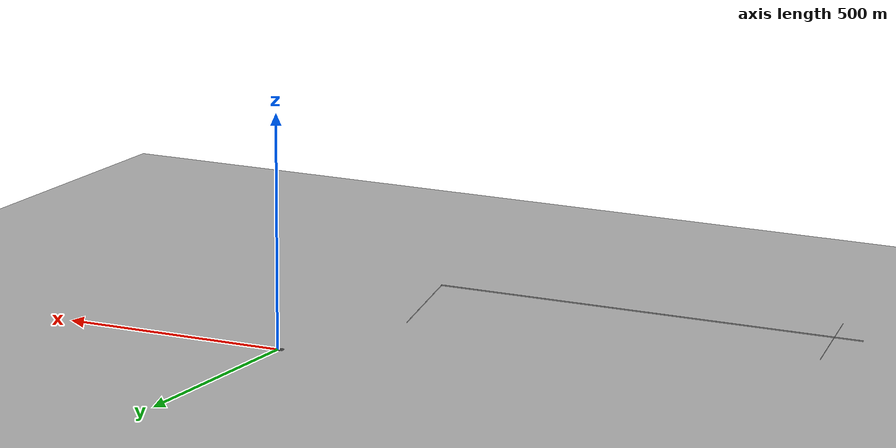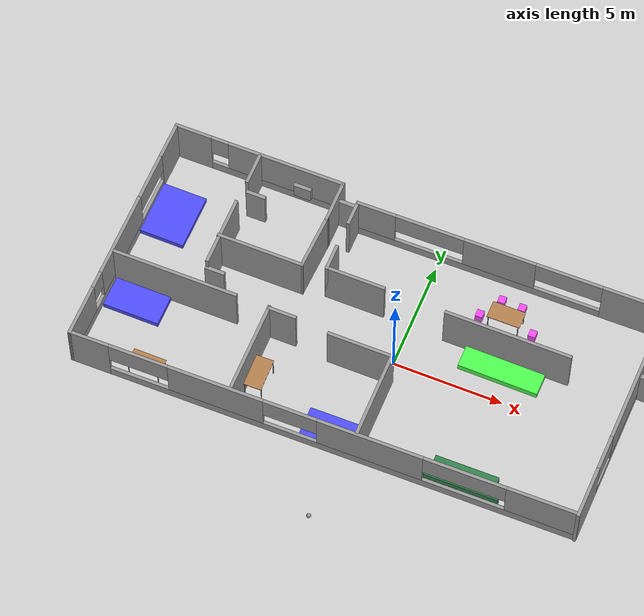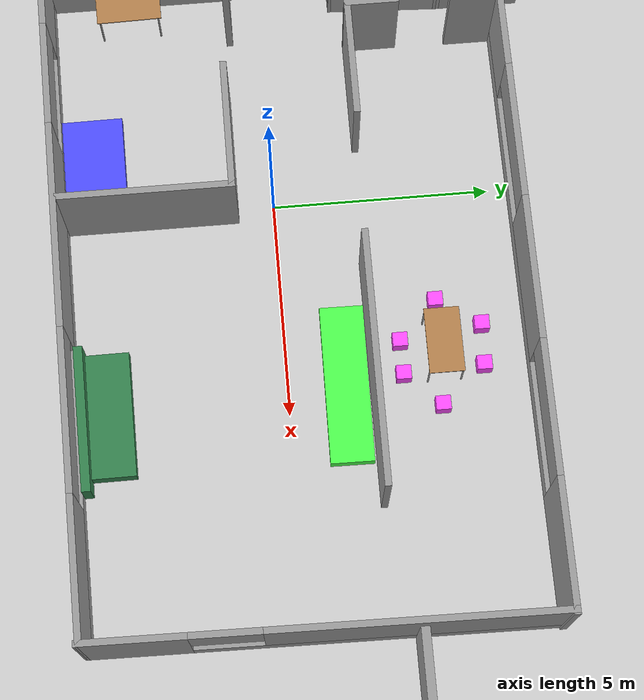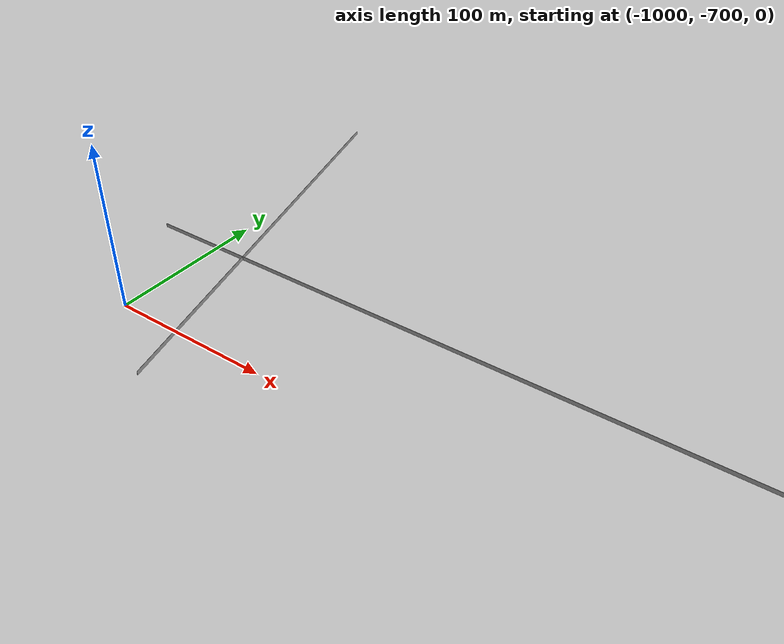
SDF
<sdf version="1.6">
 <world name="default">
  <plugin name="welcome" filename="libwelcome.so"/>
  <light name="sun" type="directional">
   <pose>0 0 10 0 -0 0</pose>
   <diffuse>0.8 0.8 0.8 1</diffuse>
   <specular>0.2 0.2 0.2 1</specular>
   <attenuation>
    <range>1000</range>
    <constant>0.9</constant>
    <linear>0.01</linear>
    <quadratic>0.001</quadratic>
   </attenuation>
   <direction>-0.5 0.1 -0.9</direction>
   <spot><inner_angle>0</inner_angle><outer_angle>0</outer_angle><falloff>0</falloff></spot>
  </light>
  <model name="ground_plane">
   <static>1</static>
   <link name="link">
    <collision name="collision">
     <geometry><plane><normal>0 0 1</normal><size>100 100</size></plane></geometry>
     <surface><friction><ode><mu>100</mu><mu2>50</mu2></ode></friction></surface>
    </collision>
    <visual name="visual">
     <cast_shadows>0</cast_shadows>
     <geometry><plane><normal>0 0 1</normal><size>100 100</size></plane></geometry>
     <material>
      <script><uri>file://media/materials/scripts/gazebo.material</uri><name>Gazebo/Grey</name></script>
     </material>
    </visual>
   </link>
  </model>
  <gravity>0 0 -9.8</gravity>
  <magnetic_field>6e-06 2.3e-05 -4.2e-05</magnetic_field>
  <atmosphere type="adiabatic"/>
  <physics name="default_physics" default="0" type="ode">
   <max_step_size>0.001</max_step_size>
   <real_time_factor>1</real_time_factor>
   <real_time_update_rate>1000</real_time_update_rate>
  </physics>
  <scene><ambient>0.4 0.4 0.4 1</ambient><background>0.7 0.7 0.7 1</background><shadows>1</shadows></scene>
  <spherical_coordinates>
   <surface_model>EARTH_WGS84</surface_model>
   <latitude_deg>0</latitude_deg>
   <longitude_deg>0</longitude_deg>
   <elevation>0</elevation>
   <heading_deg>0</heading_deg>
  </spherical_coordinates>
  <model name="home_0">
   <pose>-546.929 -525.599 0 0 -0 0</pose>
   <link name="Wall_34">
    <collision name="Wall_34_Collision">
     <geometry><box><size>298.25 0.15 2.5</size></box></geometry>
     <pose>0 0 1.25 0 -0 0</pose>
    </collision>
    <visual name="Wall_34_Visual">
     <pose>0 0 1.25 0 -0 0</pose>
     <geometry><box><size>298.25 0.15 2.5</size></box></geometry>
     <material>
      <script><uri>file://media/materials/scripts/gazebo.material</uri><name>Gazebo/Grey</name></script>
      <ambient>1 1 1 1</ambient>
     </material>
     <meta><layer>0</layer></meta>
    </visual>
    <pose>-440.493 -66.4877 0 0 0 -1.309</pose>
   </link>
   <link name="Wall_36">
    <collision name="Wall_36_Collision">
     <geometry><box><size>994.5 0.15 2.5</size></box></geometry>
     <pose>0 0 1.25 0 -0 0</pose>
    </collision>
    <visual name="Wall_36_Visual">
     <pose>0 0 1.25 0 -0 0</pose>
     <geometry><box><size>994.5 0.15 2.5</size></box></geometry>
     <material>
      <script><uri>file://media/materials/scripts/gazebo.material</uri><name>Gazebo/Grey</name></script>
      <ambient>1 1 1 1</ambient>
     </material>
     <meta><layer>0</layer></meta>
    </visual>
    <pose>-0.008396 -101.39 0 0 -0 0</pose>
   </link>
   <link name="Wall_37">
    <collision name="Wall_37_Collision">
     <geometry><box><size>323 0.15 2.5</size></box></geometry>
     <pose>0 0 1.25 0 -0 0</pose>
    </collision>
    <visual name="Wall_37_Visual">
     <pose>0 0 1.25 0 -0 0</pose>
     <geometry><box><size>323 0.15 2.5</size></box></geometry>
     <material>
      <script><uri>file://media/materials/scripts/gazebo.material</uri><name>Gazebo/Grey</name></script>
      <ambient>1 1 1 1</ambient>
     </material>
     <meta><layer>0</layer></meta>
    </visual>
    <pose>455.387 54.5343 0 0 -0 1.8326</pose>
   </link>
   <static>1</static>
  </model>
  <model name="table">
   <static>1</static>
   <link name="link">
    <collision name="surface">
     <pose>0 0 1 0 -0 0</pose>
     <geometry><box><size>1.5 0.8 0.03</size></box></geometry>
     <surface><friction><ode><mu>0.6</mu><mu2>0.6</mu2></ode></friction></surface>
    </collision>
    <visual name="visual1">
     <pose>0 0 1 0 -0 0</pose>
     <geometry><box><size>1.5 0.8 0.03</size></box></geometry>
     <material>
      <script><uri>file://media/materials/scripts/gazebo.material</uri><name>Gazebo/Wood</name></script>
     </material>
    </visual>
    <collision name="front_left_leg">
     <pose>0.68 0.38 0.5 0 -0 0</pose>
     <geometry><cylinder><radius>0.02</radius><length>1</length></cylinder></geometry>
    </collision>
    <visual name="front_left_leg">
     <pose>0.68 0.38 0.5 0 -0 0</pose>
     <geometry><cylinder><radius>0.02</radius><length>1</length></cylinder></geometry>
     <material>
      <script><uri>file://media/materials/scripts/gazebo.material</uri><name>Gazebo/Grey</name></script>
     </material>
    </visual>
    <collision name="front_right_leg">
     <pose>0.68 -0.38 0.5 0 -0 0</pose>
     <geometry><cylinder><radius>0.02</radius><length>1</length></cylinder></geometry>
    </collision>
    <visual name="front_right_leg">
     <pose>0.68 -0.38 0.5 0 -0 0</pose>
     <geometry><cylinder><radius>0.02</radius><length>1</length></cylinder></geometry>
     <material>
      <script><uri>file://media/materials/scripts/gazebo.material</uri><name>Gazebo/Grey</name></script>
     </material>
    </visual>
    <collision name="back_right_leg">
     <pose>-0.68 -0.38 0.5 0 -0 0</pose>
     <geometry><cylinder><radius>0.02</radius><length>1</length></cylinder></geometry>
    </collision>
    <visual name="back_right_leg">
     <pose>-0.68 -0.38 0.5 0 -0 0</pose>
     <geometry><cylinder><radius>0.02</radius><length>1</length></cylinder></geometry>
     <material>
      <script><uri>file://media/materials/scripts/gazebo.material</uri><name>Gazebo/Grey</name></script>
     </material>
    </visual>
    <collision name="back_left_leg">
     <pose>-0.68 0.38 0.5 0 -0 0</pose>
     <geometry><cylinder><radius>0.02</radius><length>1</length></cylinder></geometry>
    </collision>
    <visual name="back_left_leg">
     <pose>-0.68 0.38 0.5 0 -0 0</pose>
     <geometry><cylinder><radius>0.02</radius><length>1</length></cylinder></geometry>
     <material>
      <script><uri>file://media/materials/scripts/gazebo.material</uri><name>Gazebo/Grey</name></script>
     </material>
    </visual>
   </link>
   <pose>3.77671 3.56067 0 0 -0 0</pose>
  </model>
  <model name="unit_box_1">
   <link name="link">
    <pose>-0.362348 -0.121624 0 0 -0 0</pose>
    <inertial>
     <mass>1</mass>
     <inertia>
      <ixx>0.166667</ixx>
      <ixy>0</ixy>
      <ixz>0</ixz>
      <iyy>0.166667</iyy>
      <iyz>0</iyz>
      <izz>0.166667</izz>
     </inertia>
    </inertial>
    <visual name="visual">
     <geometry><box><size>0.32527 0.342485 0.391926</size></box></geometry>
     <material>
      <script><name>Gazebo/Grey</name><uri>file://media/materials/scripts/gazebo.material</uri></script>
      <shader type="pixel"><normal_map>__default__</normal_map></shader>
      <ambient>1 0.3 1 1</ambient>
      <diffuse>0.7 0.7 0.7 1</diffuse>
      <specular>0.01 0.01 0.01 1</specular>
      <emissive>0 0 0 1</emissive>
     </material>
    </visual>
    <collision name="collision">
     <geometry><box><size>0.32527 0.342485 0.391926</size></box></geometry>
     <surface>
      <friction>
       <ode><mu>1</mu><mu2>1</mu2><fdir1>0 0 0</fdir1><slip1>0</slip1><slip2>0</slip2></ode>
       <torsional>
        <coefficient>1</coefficient>
        <patch_radius>0</patch_radius>
        <surface_radius>0</surface_radius>
        <use_patch_radius>1</use_patch_radius>
        <ode><slip>0</slip></ode>
       </torsional>
      </friction>
      <bounce><restitution_coefficient>0</restitution_coefficient><threshold>1e+06</threshold></bounce>
      <contact>
       <collide_without_contact>0</collide_without_contact>
       <collide_without_contact_bitmask>1</collide_without_contact_bitmask>
       <collide_bitmask>1</collide_bitmask>
       <ode>
        <soft_cfm>0</soft_cfm>
        <soft_erp>0.2</soft_erp>
        <kp>1e+13</kp>
        <kd>1</kd>
        <max_vel>0.01</max_vel>
        <min_depth>0</min_depth>
       </ode>
       <bullet>
        <split_impulse>1</split_impulse>
        <split_impulse_penetration_threshold>-0.01</split_impulse_penetration_threshold>
        <soft_cfm>0</soft_cfm>
        <soft_erp>0.2</soft_erp>
        <kp>1e+13</kp>
        <kd>1</kd>
       </bullet>
      </contact>
     </surface>
    </collision>
   </link>
   <link name="link_clone">
    <pose>-1.14011 -0.94502 0 0 -0 0</pose>
    <inertial>
     <mass>1</mass>
     <inertia>
      <ixx>0.166667</ixx>
      <ixy>0</ixy>
      <ixz>0</ixz>
      <iyy>0.166667</iyy>
      <iyz>0</iyz>
      <izz>0.166667</izz>
     </inertia>
    </inertial>
    <visual name="visual">
     <geometry><box><size>0.32527 0.342485 0.391926</size></box></geometry>
     <material>
      <script><name>Gazebo/Grey</name><uri>file://media/materials/scripts/gazebo.material</uri></script>
      <shader type="pixel"><normal_map>__default__</normal_map></shader>
      <ambient>1 0.3 1 1</ambient>
      <diffuse>0.7 0.7 0.7 1</diffuse>
      <specular>0.01 0.01 0.01 1</specular>
      <emissive>0 0 0 1</emissive>
     </material>
    </visual>
    <collision name="collision">
     <geometry><box><size>0.32527 0.342485 0.391926</size></box></geometry>
     <surface>
      <friction>
       <ode><mu>1</mu><mu2>1</mu2><fdir1>0 0 0</fdir1><slip1>0</slip1><slip2>0</slip2></ode>
       <torsional>
        <coefficient>1</coefficient>
        <patch_radius>0</patch_radius>
        <surface_radius>0</surface_radius>
        <use_patch_radius>1</use_patch_radius>
        <ode><slip>0</slip></ode>
       </torsional>
      </friction>
      <bounce><restitution_coefficient>0</restitution_coefficient><threshold>1e+06</threshold></bounce>
      <contact>
       <collide_without_contact>0</collide_without_contact>
       <collide_without_contact_bitmask>1</collide_without_contact_bitmask>
       <collide_bitmask>1</collide_bitmask>
       <ode>
        <soft_cfm>0</soft_cfm>
        <soft_erp>0.2</soft_erp>
        <kp>1e+13</kp>
        <kd>1</kd>
        <max_vel>0.01</max_vel>
        <min_depth>0</min_depth>
       </ode>
       <bullet>
        <split_impulse>1</split_impulse>
        <split_impulse_penetration_threshold>-0.01</split_impulse_penetration_threshold>
        <soft_cfm>0</soft_cfm>
        <soft_erp>0.2</soft_erp>
        <kp>1e+13</kp>
        <kd>1</kd>
       </bullet>
      </contact>
     </surface>
    </collision>
   </link>
   <link name="link_clone_0">
    <pose>-1.91265 -0.960406 0 0 -0 0</pose>
    <inertial>
     <mass>1</mass>
     <inertia>
      <ixx>0.166667</ixx>
      <ixy>0</ixy>
      <ixz>0</ixz>
      <iyy>0.166667</iyy>
      <iyz>0</iyz>
      <izz>0.166667</izz>
     </inertia>
    </inertial>
    <visual name="visual">
     <geometry><box><size>0.32527 0.342485 0.391926</size></box></geometry>
     <material>
      <script><name>Gazebo/Grey</name><uri>file://media/materials/scripts/gazebo.material</uri></script>
      <shader type="pixel"><normal_map>__default__</normal_map></shader>
      <ambient>1 0.3 1 1</ambient>
      <diffuse>0.7 0.7 0.7 1</diffuse>
      <specular>0.01 0.01 0.01 1</specular>
      <emissive>0 0 0 1</emissive>
     </material>
    </visual>
    <collision name="collision">
     <geometry><box><size>0.32527 0.342485 0.391926</size></box></geometry>
     <surface>
      <friction>
       <ode><mu>1</mu><mu2>1</mu2><fdir1>0 0 0</fdir1><slip1>0</slip1><slip2>0</slip2></ode>
       <torsional>
        <coefficient>1</coefficient>
        <patch_radius>0</patch_radius>
        <surface_radius>0</surface_radius>
        <use_patch_radius>1</use_patch_radius>
        <ode><slip>0</slip></ode>
       </torsional>
      </friction>
      <bounce><restitution_coefficient>0</restitution_coefficient><threshold>1e+06</threshold></bounce>
      <contact>
       <collide_without_contact>0</collide_without_contact>
       <collide_without_contact_bitmask>1</collide_without_contact_bitmask>
       <collide_bitmask>1</collide_bitmask>
       <ode>
        <soft_cfm>0</soft_cfm>
        <soft_erp>0.2</soft_erp>
        <kp>1e+13</kp>
        <kd>1</kd>
        <max_vel>0.01</max_vel>
        <min_depth>0</min_depth>
       </ode>
       <bullet>
        <split_impulse>1</split_impulse>
        <split_impulse_penetration_threshold>-0.01</split_impulse_penetration_threshold>
        <soft_cfm>0</soft_cfm>
        <soft_erp>0.2</soft_erp>
        <kp>1e+13</kp>
        <kd>1</kd>
       </bullet>
      </contact>
     </surface>
    </collision>
   </link>
   <link name="link_clone_1">
    <pose>-2.81439 -0.071099 0 0 -0 0</pose>
    <inertial>
     <mass>1</mass>
     <inertia>
      <ixx>0.166667</ixx>
      <ixy>0</ixy>
      <ixz>0</ixz>
      <iyy>0.166667</iyy>
      <iyz>0</iyz>
      <izz>0.166667</izz>
     </inertia>
    </inertial>
    <visual name="visual">
     <geometry><box><size>0.32527 0.342485 0.391926</size></box></geometry>
     <material>
      <script><name>Gazebo/Grey</name><uri>file://media/materials/scripts/gazebo.material</uri></script>
      <shader type="pixel"><normal_map>__default__</normal_map></shader>
      <ambient>1 0.3 1 1</ambient>
      <diffuse>0.7 0.7 0.7 1</diffuse>
      <specular>0.01 0.01 0.01 1</specular>
      <emissive>0 0 0 1</emissive>
     </material>
    </visual>
    <collision name="collision">
     <geometry><box><size>0.32527 0.342485 0.391926</size></box></geometry>
     <surface>
      <friction>
       <ode><mu>1</mu><mu2>1</mu2><fdir1>0 0 0</fdir1><slip1>0</slip1><slip2>0</slip2></ode>
       <torsional>
        <coefficient>1</coefficient>
        <patch_radius>0</patch_radius>
        <surface_radius>0</surface_radius>
        <use_patch_radius>1</use_patch_radius>
        <ode><slip>0</slip></ode>
       </torsional>
      </friction>
      <bounce><restitution_coefficient>0</restitution_coefficient><threshold>1e+06</threshold></bounce>
      <contact>
       <collide_without_contact>0</collide_without_contact>
       <collide_without_contact_bitmask>1</collide_without_contact_bitmask>
       <collide_bitmask>1</collide_bitmask>
       <ode>
        <soft_cfm>0</soft_cfm>
        <soft_erp>0.2</soft_erp>
        <kp>1e+13</kp>
        <kd>1</kd>
        <max_vel>0.01</max_vel>
        <min_depth>0</min_depth>
       </ode>
       <bullet>
        <split_impulse>1</split_impulse>
        <split_impulse_penetration_threshold>-0.01</split_impulse_penetration_threshold>
        <soft_cfm>0</soft_cfm>
        <soft_erp>0.2</soft_erp>
        <kp>1e+13</kp>
        <kd>1</kd>
       </bullet>
      </contact>
     </surface>
    </collision>
   </link>
   <link name="link_clone_2">
    <pose>-2.17183 0.931538 0 0 -0 0</pose>
    <inertial>
     <mass>1</mass>
     <inertia>
      <ixx>0.166667</ixx>
      <ixy>0</ixy>
      <ixz>0</ixz>
      <iyy>0.166667</iyy>
      <iyz>0</iyz>
      <izz>0.166667</izz>
     </inertia>
    </inertial>
    <visual name="visual">
     <geometry><box><size>0.32527 0.342485 0.391926</size></box></geometry>
     <material>
      <script><name>Gazebo/Grey</name><uri>file://media/materials/scripts/gazebo.material</uri></script>
      <shader type="pixel"><normal_map>__default__</normal_map></shader>
      <ambient>1 0.3 1 1</ambient>
      <diffuse>0.7 0.7 0.7 1</diffuse>
      <specular>0.01 0.01 0.01 1</specular>
      <emissive>0 0 0 1</emissive>
     </material>
    </visual>
    <collision name="collision">
     <geometry><box><size>0.32527 0.342485 0.391926</size></box></geometry>
     <surface>
      <friction>
       <ode><mu>1</mu><mu2>1</mu2><fdir1>0 0 0</fdir1><slip1>0</slip1><slip2>0</slip2></ode>
       <torsional>
        <coefficient>1</coefficient>
        <patch_radius>0</patch_radius>
        <surface_radius>0</surface_radius>
        <use_patch_radius>1</use_patch_radius>
        <ode><slip>0</slip></ode>
       </torsional>
      </friction>
      <bounce><restitution_coefficient>0</restitution_coefficient><threshold>1e+06</threshold></bounce>
      <contact>
       <collide_without_contact>0</collide_without_contact>
       <collide_without_contact_bitmask>1</collide_without_contact_bitmask>
       <collide_bitmask>1</collide_bitmask>
       <ode>
        <soft_cfm>0</soft_cfm>
        <soft_erp>0.2</soft_erp>
        <kp>1e+13</kp>
        <kd>1</kd>
        <max_vel>0.01</max_vel>
        <min_depth>0</min_depth>
       </ode>
       <bullet>
        <split_impulse>1</split_impulse>
        <split_impulse_penetration_threshold>-0.01</split_impulse_penetration_threshold>
        <soft_cfm>0</soft_cfm>
        <soft_erp>0.2</soft_erp>
        <kp>1e+13</kp>
        <kd>1</kd>
       </bullet>
      </contact>
     </surface>
    </collision>
   </link>
   <link name="link_clone_3">
    <pose>-1.22615 0.898021 0 0 -0 0</pose>
    <inertial>
     <mass>1</mass>
     <inertia>
      <ixx>0.166667</ixx>
      <ixy>0</ixy>
      <ixz>0</ixz>
      <iyy>0.166667</iyy>
      <iyz>0</iyz>
      <izz>0.166667</izz>
     </inertia>
    </inertial>
    <visual name="visual">
     <geometry><box><size>0.32527 0.342485 0.391926</size></box></geometry>
     <material>
      <script><name>Gazebo/Grey</name><uri>file://media/materials/scripts/gazebo.material</uri></script>
      <shader type="pixel"><normal_map>__default__</normal_map></shader>
      <ambient>1 0.3 1 1</ambient>
      <diffuse>0.7 0.7 0.7 1</diffuse>
      <specular>0.01 0.01 0.01 1</specular>
      <emissive>0 0 0 1</emissive>
     </material>
    </visual>
    <collision name="collision">
     <geometry><box><size>0.32527 0.342485 0.391926</size></box></geometry>
     <surface>
      <friction>
       <ode><mu>1</mu><mu2>1</mu2><fdir1>0 0 0</fdir1><slip1>0</slip1><slip2>0</slip2></ode>
       <torsional>
        <coefficient>1</coefficient>
        <patch_radius>0</patch_radius>
        <surface_radius>0</surface_radius>
        <use_patch_radius>1</use_patch_radius>
        <ode><slip>0</slip></ode>
       </torsional>
      </friction>
      <bounce><restitution_coefficient>0</restitution_coefficient><threshold>1e+06</threshold></bounce>
      <contact>
       <collide_without_contact>0</collide_without_contact>
       <collide_without_contact_bitmask>1</collide_without_contact_bitmask>
       <collide_bitmask>1</collide_bitmask>
       <ode>
        <soft_cfm>0</soft_cfm>
        <soft_erp>0.2</soft_erp>
        <kp>1e+13</kp>
        <kd>1</kd>
        <max_vel>0.01</max_vel>
        <min_depth>0</min_depth>
       </ode>
       <bullet>
        <split_impulse>1</split_impulse>
        <split_impulse_penetration_threshold>-0.01</split_impulse_penetration_threshold>
        <soft_cfm>0</soft_cfm>
        <soft_erp>0.2</soft_erp>
        <kp>1e+13</kp>
        <kd>1</kd>
       </bullet>
      </contact>
     </surface>
    </collision>
   </link>
   <static>0</static>
   <pose>5.42518 3.58061 0.195963 0 -0 0</pose>
  </model>
  <model name="TV_stand">
   <link name="link">
    <inertial>
     <mass>1.21546</mass>
     <inertia><ixx>0.112011</ixx><ixy>0</ixy><ixz>0</ixz><iyy>1.34483</iyy><iyz>0</iyz><izz>1.4354</izz></inertia>
    </inertial>
    <visual name="visual">
     <geometry><box><size>3.62925 1 0.32537</size></box></geometry>
     <material>
      <script><name>Gazebo/Grey</name><uri>file://media/materials/scripts/gazebo.material</uri></script>
      <shader type="pixel"><normal_map>__default__</normal_map></shader>
      <ambient>0.3 1 0.3 0</ambient>
      <diffuse>0.7 0.7 0.7 1</diffuse>
      <specular>0.01 0.01 0.01 1</specular>
      <emissive>0 0 0 1</emissive>
     </material>
    </visual>
    <collision name="collision">
     <geometry><box><size>3.62925 1 0.32537</size></box></geometry>
     <surface>
      <friction>
       <ode><mu>1</mu><mu2>1</mu2><fdir1>0 0 0</fdir1><slip1>0</slip1><slip2>0</slip2></ode>
       <torsional>
        <coefficient>1</coefficient>
        <patch_radius>0</patch_radius>
        <surface_radius>0</surface_radius>
        <use_patch_radius>1</use_patch_radius>
        <ode><slip>0</slip></ode>
       </torsional>
      </friction>
      <bounce><restitution_coefficient>0</restitution_coefficient><threshold>1e+06</threshold></bounce>
      <contact>
       <collide_without_contact>0</collide_without_contact>
       <collide_without_contact_bitmask>1</collide_without_contact_bitmask>
       <collide_bitmask>1</collide_bitmask>
       <ode>
        <soft_cfm>0</soft_cfm>
        <soft_erp>0.2</soft_erp>
        <kp>1e+13</kp>
        <kd>1</kd>
        <max_vel>0.01</max_vel>
        <min_depth>0</min_depth>
       </ode>
       <bullet>
        <split_impulse>1</split_impulse>
        <split_impulse_penetration_threshold>-0.01</split_impulse_penetration_threshold>
        <soft_cfm>0</soft_cfm>
        <soft_erp>0.2</soft_erp>
        <kp>1e+13</kp>
        <kd>1</kd>
       </bullet>
      </contact>
     </surface>
    </collision>
   </link>
   <static>0</static>
   <pose>4.44126 1.33199 0.16268 -1e-05 -0 -0.009087</pose>
  </model>
  <model name="couch_base">
   <link name="link">
    <inertial>
     <mass>1</mass>
     <inertia>
      <ixx>0.166667</ixx>
      <ixy>0</ixy>
      <ixz>0</ixz>
      <iyy>0.166667</iyy>
      <iyz>0</iyz>
      <izz>0.166667</izz>
     </inertia>
    </inertial>
    <visual name="visual">
     <geometry><box><size>2.85561 1 0.415231</size></box></geometry>
     <material>
      <script><name>Gazebo/Grey</name><uri>file://media/materials/scripts/gazebo.material</uri></script>
      <shader type="pixel"><normal_map>__default__</normal_map></shader>
      <ambient>0.2 0.5 0.3 1</ambient>
      <diffuse>0.7 0.7 0.7 1</diffuse>
      <specular>0.01 0.01 0.01 1</specular>
      <emissive>0 0 0 1</emissive>
     </material>
    </visual>
    <collision name="collision">
     <geometry><box><size>2.85561 1 0.415231</size></box></geometry>
     <surface>
      <friction>
       <ode><mu>1</mu><mu2>1</mu2><fdir1>0 0 0</fdir1><slip1>0</slip1><slip2>0</slip2></ode>
       <torsional>
        <coefficient>1</coefficient>
        <patch_radius>0</patch_radius>
        <surface_radius>0</surface_radius>
        <use_patch_radius>1</use_patch_radius>
        <ode><slip>0</slip></ode>
       </torsional>
      </friction>
      <bounce><restitution_coefficient>0</restitution_coefficient><threshold>1e+06</threshold></bounce>
      <contact>
       <collide_without_contact>0</collide_without_contact>
       <collide_without_contact_bitmask>1</collide_without_contact_bitmask>
       <collide_bitmask>1</collide_bitmask>
       <ode>
        <soft_cfm>0</soft_cfm>
        <soft_erp>0.2</soft_erp>
        <kp>1e+13</kp>
        <kd>1</kd>
        <max_vel>0.01</max_vel>
        <min_depth>0</min_depth>
       </ode>
       <bullet>
        <split_impulse>1</split_impulse>
        <split_impulse_penetration_threshold>-0.01</split_impulse_penetration_threshold>
        <soft_cfm>0</soft_cfm>
        <soft_erp>0.2</soft_erp>
        <kp>1e+13</kp>
        <kd>1</kd>
       </bullet>
      </contact>
     </surface>
    </collision>
   </link>
   <static>0</static>
   <pose>4.77273 -4.01404 0.207375 0 -0.000169 0.008021</pose>
  </model>
  <model name="couch_back">
   <link name="link">
    <inertial>
     <mass>1</mass>
     <inertia>
      <ixx>0.166667</ixx>
      <ixy>0</ixy>
      <ixz>0</ixz>
      <iyy>0.166667</iyy>
      <iyz>0</iyz>
      <izz>0.166667</izz>
     </inertia>
    </inertial>
    <visual name="visual">
     <geometry><box><size>3.32313 0.208176 0.825723</size></box></geometry>
     <material>
      <script><name>Gazebo/Grey</name><uri>file://media/materials/scripts/gazebo.material</uri></script>
      <shader type="pixel"><normal_map>__default__</normal_map></shader>
      <ambient>0.2 0.5 0.3 1</ambient>
      <diffuse>0.7 0.7 0.7 1</diffuse>
      <specular>0.01 0.01 0.01 1</specular>
      <emissive>0 0 0 1</emissive>
     </material>
    </visual>
    <collision name="collision">
     <geometry><box><size>3.32313 0.208176 0.825723</size></box></geometry>
     <surface>
      <friction>
       <ode><mu>1</mu><mu2>1</mu2><fdir1>0 0 0</fdir1><slip1>0</slip1><slip2>0</slip2></ode>
       <torsional>
        <coefficient>1</coefficient>
        <patch_radius>0</patch_radius>
        <surface_radius>0</surface_radius>
        <use_patch_radius>1</use_patch_radius>
        <ode><slip>0</slip></ode>
       </torsional>
      </friction>
      <bounce><restitution_coefficient>0</restitution_coefficient><threshold>1e+06</threshold></bounce>
      <contact>
       <collide_without_contact>0</collide_without_contact>
       <collide_without_contact_bitmask>1</collide_without_contact_bitmask>
       <collide_bitmask>1</collide_bitmask>
       <ode>
        <soft_cfm>0</soft_cfm>
        <soft_erp>0.2</soft_erp>
        <kp>1e+13</kp>
        <kd>1</kd>
        <max_vel>0.01</max_vel>
        <min_depth>0</min_depth>
       </ode>
       <bullet>
        <split_impulse>1</split_impulse>
        <split_impulse_penetration_threshold>-0.01</split_impulse_penetration_threshold>
        <soft_cfm>0</soft_cfm>
        <soft_erp>0.2</soft_erp>
        <kp>1e+13</kp>
        <kd>1</kd>
       </bullet>
      </contact>
     </surface>
    </collision>
   </link>
   <static>0</static>
   <pose>4.88292 -4.6211 0.412517 7e-06 -0.000208 0.010679</pose>
  </model>
  <model name="table_0">
   <static>1</static>
   <link name="link">
    <collision name="surface">
     <pose>0 0 1 0 -0 0</pose>
     <geometry><box><size>1.5 0.8 0.03</size></box></geometry>
     <surface><friction><ode><mu>0.6</mu><mu2>0.6</mu2></ode></friction></surface>
    </collision>
    <visual name="visual1">
     <pose>0 0 1 0 -0 0</pose>
     <geometry><box><size>1.5 0.8 0.03</size></box></geometry>
     <material>
      <script><uri>file://media/materials/scripts/gazebo.material</uri><name>Gazebo/Wood</name></script>
     </material>
    </visual>
    <collision name="front_left_leg">
     <pose>0.68 0.38 0.5 0 -0 0</pose>
     <geometry><cylinder><radius>0.02</radius><length>1</length></cylinder></geometry>
    </collision>
    <visual name="front_left_leg">
     <pose>0.68 0.38 0.5 0 -0 0</pose>
     <geometry><cylinder><radius>0.02</radius><length>1</length></cylinder></geometry>
     <material>
      <script><uri>file://media/materials/scripts/gazebo.material</uri><name>Gazebo/Grey</name></script>
     </material>
    </visual>
    <collision name="front_right_leg">
     <pose>0.68 -0.38 0.5 0 -0 0</pose>
     <geometry><cylinder><radius>0.02</radius><length>1</length></cylinder></geometry>
    </collision>
    <visual name="front_right_leg">
     <pose>0.68 -0.38 0.5 0 -0 0</pose>
     <geometry><cylinder><radius>0.02</radius><length>1</length></cylinder></geometry>
     <material>
      <script><uri>file://media/materials/scripts/gazebo.material</uri><name>Gazebo/Grey</name></script>
     </material>
    </visual>
    <collision name="back_right_leg">
     <pose>-0.68 -0.38 0.5 0 -0 0</pose>
     <geometry><cylinder><radius>0.02</radius><length>1</length></cylinder></geometry>
    </collision>
    <visual name="back_right_leg">
     <pose>-0.68 -0.38 0.5 0 -0 0</pose>
     <geometry><cylinder><radius>0.02</radius><length>1</length></cylinder></geometry>
     <material>
      <script><uri>file://media/materials/scripts/gazebo.material</uri><name>Gazebo/Grey</name></script>
     </material>
    </visual>
    <collision name="back_left_leg">
     <pose>-0.68 0.38 0.5 0 -0 0</pose>
     <geometry><cylinder><radius>0.02</radius><length>1</length></cylinder></geometry>
    </collision>
    <visual name="back_left_leg">
     <pose>-0.68 0.38 0.5 0 -0 0</pose>
     <geometry><cylinder><radius>0.02</radius><length>1</length></cylinder></geometry>
     <material>
      <script><uri>file://media/materials/scripts/gazebo.material</uri><name>Gazebo/Grey</name></script>
     </material>
    </visual>
   </link>
   <pose>-9.54504 -4.40497 0 0 -0 0</pose>
  </model>
  <model name="bed_1">
   <link name="link">
    <inertial>
     <mass>1</mass>
     <inertia>
      <ixx>0.166667</ixx>
      <ixy>0</ixy>
      <ixz>0</ixz>
      <iyy>0.166667</iyy>
      <iyz>0</iyz>
      <izz>0.166667</izz>
     </inertia>
    </inertial>
    <visual name="visual">
     <geometry><box><size>1.40955 2.56695 0.267057</size></box></geometry>
     <material>
      <script><name>Gazebo/Grey</name><uri>file://media/materials/scripts/gazebo.material</uri></script>
      <shader type="pixel"><normal_map>__default__</normal_map></shader>
      <ambient>0.3 0.3 1 0</ambient>
      <diffuse>0.7 0.7 0.7 1</diffuse>
      <specular>0.01 0.01 0.01 1</specular>
      <emissive>0 0 0 1</emissive>
     </material>
    </visual>
    <collision name="collision">
     <geometry><box><size>1.40955 2.56695 0.267057</size></box></geometry>
     <surface>
      <friction>
       <ode><mu>1</mu><mu2>1</mu2><fdir1>0 0 0</fdir1><slip1>0</slip1><slip2>0</slip2></ode>
       <torsional>
        <coefficient>1</coefficient>
        <patch_radius>0</patch_radius>
        <surface_radius>0</surface_radius>
        <use_patch_radius>1</use_patch_radius>
        <ode><slip>0</slip></ode>
       </torsional>
      </friction>
      <bounce><restitution_coefficient>0</restitution_coefficient><threshold>1e+06</threshold></bounce>
      <contact>
       <collide_without_contact>0</collide_without_contact>
       <collide_without_contact_bitmask>1</collide_without_contact_bitmask>
       <collide_bitmask>1</collide_bitmask>
       <ode>
        <soft_cfm>0</soft_cfm>
        <soft_erp>0.2</soft_erp>
        <kp>1e+13</kp>
        <kd>1</kd>
        <max_vel>0.01</max_vel>
        <min_depth>0</min_depth>
       </ode>
       <bullet>
        <split_impulse>1</split_impulse>
        <split_impulse_penetration_threshold>-0.01</split_impulse_penetration_threshold>
        <soft_cfm>0</soft_cfm>
        <soft_erp>0.2</soft_erp>
        <kp>1e+13</kp>
        <kd>1</kd>
       </bullet>
      </contact>
     </surface>
    </collision>
   </link>
   <static>0</static>
   <pose>-11.3281 -1.47696 0.133524 3.14159 7e-06 1.56809</pose>
  </model>
  <model name="table_1">
   <static>1</static>
   <link name="link">
    <collision name="surface">
     <pose>0 0 1 0 -0 0</pose>
     <geometry><box><size>1.5 0.8 0.03</size></box></geometry>
     <surface><friction><ode><mu>0.6</mu><mu2>0.6</mu2></ode></friction></surface>
    </collision>
    <visual name="visual1">
     <pose>0 0 1 0 -0 0</pose>
     <geometry><box><size>1.5 0.8 0.03</size></box></geometry>
     <material>
      <script><uri>file://media/materials/scripts/gazebo.material</uri><name>Gazebo/Wood</name></script>
     </material>
    </visual>
    <collision name="front_left_leg">
     <pose>0.68 0.38 0.5 0 -0 0</pose>
     <geometry><cylinder><radius>0.02</radius><length>1</length></cylinder></geometry>
    </collision>
    <visual name="front_left_leg">
     <pose>0.68 0.38 0.5 0 -0 0</pose>
     <geometry><cylinder><radius>0.02</radius><length>1</length></cylinder></geometry>
     <material>
      <script><uri>file://media/materials/scripts/gazebo.material</uri><name>Gazebo/Grey</name></script>
     </material>
    </visual>
    <collision name="front_right_leg">
     <pose>0.68 -0.38 0.5 0 -0 0</pose>
     <geometry><cylinder><radius>0.02</radius><length>1</length></cylinder></geometry>
    </collision>
    <visual name="front_right_leg">
     <pose>0.68 -0.38 0.5 0 -0 0</pose>
     <geometry><cylinder><radius>0.02</radius><length>1</length></cylinder></geometry>
     <material>
      <script><uri>file://media/materials/scripts/gazebo.material</uri><name>Gazebo/Grey</name></script>
     </material>
    </visual>
    <collision name="back_right_leg">
     <pose>-0.68 -0.38 0.5 0 -0 0</pose>
     <geometry><cylinder><radius>0.02</radius><length>1</length></cylinder></geometry>
    </collision>
    <visual name="back_right_leg">
     <pose>-0.68 -0.38 0.5 0 -0 0</pose>
     <geometry><cylinder><radius>0.02</radius><length>1</length></cylinder></geometry>
     <material>
      <script><uri>file://media/materials/scripts/gazebo.material</uri><name>Gazebo/Grey</name></script>
     </material>
    </visual>
    <collision name="back_left_leg">
     <pose>-0.68 0.38 0.5 0 -0 0</pose>
     <geometry><cylinder><radius>0.02</radius><length>1</length></cylinder></geometry>
    </collision>
    <visual name="back_left_leg">
     <pose>-0.68 0.38 0.5 0 -0 0</pose>
     <geometry><cylinder><radius>0.02</radius><length>1</length></cylinder></geometry>
     <material>
      <script><uri>file://media/materials/scripts/gazebo.material</uri><name>Gazebo/Grey</name></script>
     </material>
    </visual>
   </link>
   <pose>-4.94599 -3.0438 0 0 0 -1.5499</pose>
  </model>
  <model name="bed_1_clone">
   <link name="link">
    <inertial>
     <mass>1</mass>
     <inertia>
      <ixx>0.166667</ixx>
      <ixy>0</ixy>
      <ixz>0</ixz>
      <iyy>0.166667</iyy>
      <iyz>0</iyz>
      <izz>0.166667</izz>
     </inertia>
    </inertial>
    <visual name="visual">
     <geometry><box><size>1.40955 2.56695 0.267057</size></box></geometry>
     <material>
      <script><name>Gazebo/Grey</name><uri>file://media/materials/scripts/gazebo.material</uri></script>
      <shader type="pixel"><normal_map>__default__</normal_map></shader>
      <ambient>0.3 0.3 1 0</ambient>
      <diffuse>0.7 0.7 0.7 1</diffuse>
      <specular>0.01 0.01 0.01 1</specular>
      <emissive>0 0 0 1</emissive>
     </material>
    </visual>
    <collision name="collision">
     <geometry><box><size>1.40955 2.56695 0.267057</size></box></geometry>
     <surface>
      <friction>
       <ode><mu>1</mu><mu2>1</mu2><fdir1>0 0 0</fdir1><slip1>0</slip1><slip2>0</slip2></ode>
       <torsional>
        <coefficient>1</coefficient>
        <patch_radius>0</patch_radius>
        <surface_radius>0</surface_radius>
        <use_patch_radius>1</use_patch_radius>
        <ode><slip>0</slip></ode>
       </torsional>
      </friction>
      <bounce><restitution_coefficient>0</restitution_coefficient><threshold>1e+06</threshold></bounce>
      <contact>
       <collide_without_contact>0</collide_without_contact>
       <collide_without_contact_bitmask>1</collide_without_contact_bitmask>
       <collide_bitmask>1</collide_bitmask>
       <ode>
        <soft_cfm>0</soft_cfm>
        <soft_erp>0.2</soft_erp>
        <kp>1e+13</kp>
        <kd>1</kd>
        <max_vel>0.01</max_vel>
        <min_depth>0</min_depth>
       </ode>
       <bullet>
        <split_impulse>1</split_impulse>
        <split_impulse_penetration_threshold>-0.01</split_impulse_penetration_threshold>
        <soft_cfm>0</soft_cfm>
        <soft_erp>0.2</soft_erp>
        <kp>1e+13</kp>
        <kd>1</kd>
       </bullet>
      </contact>
     </surface>
    </collision>
   </link>
   <static>0</static>
   <pose>-1.12625 -4.08486 0.133525 0 -5e-06 -1.56014</pose>
  </model>
  <model name="bed_master_bedroom">
   <link name="link">
    <pose>0.100094 0.123025 0 0 -0 0</pose>
    <inertial>
     <mass>1.44755</mass>
     <inertia>
      <ixx>0.803455</ixx>
      <ixy>0</ixy>
      <ixz>0</ixz>
      <iyy>0.510804</iyy>
      <iyz>0</iyz>
      <izz>1.29705</izz>
     </inertia>
    </inertial>
    <visual name="visual">
     <geometry><box><size>2.04039 2.56695 0.267057</size></box></geometry>
     <material>
      <script><name>Gazebo/Grey</name><uri>file://media/materials/scripts/gazebo.material</uri></script>
      <shader type="pixel"><normal_map>__default__</normal_map></shader>
      <ambient>0.3 0.3 1 0</ambient>
      <diffuse>0.7 0.7 0.7 1</diffuse>
      <specular>0.01 0.01 0.01 1</specular>
      <emissive>0 0 0 1</emissive>
     </material>
    </visual>
    <collision name="collision">
     <geometry><box><size>2.04039 2.56695 0.267057</size></box></geometry>
     <surface>
      <friction>
       <ode><mu>1</mu><mu2>1</mu2><fdir1>0 0 0</fdir1><slip1>0</slip1><slip2>0</slip2></ode>
       <torsional>
        <coefficient>1</coefficient>
        <patch_radius>0</patch_radius>
        <surface_radius>0</surface_radius>
        <use_patch_radius>1</use_patch_radius>
        <ode><slip>0</slip></ode>
       </torsional>
      </friction>
      <bounce><restitution_coefficient>0</restitution_coefficient><threshold>1e+06</threshold></bounce>
      <contact>
       <collide_without_contact>0</collide_without_contact>
       <collide_without_contact_bitmask>1</collide_without_contact_bitmask>
       <collide_bitmask>1</collide_bitmask>
       <ode>
        <soft_cfm>0</soft_cfm>
        <soft_erp>0.2</soft_erp>
        <kp>1e+13</kp>
        <kd>1</kd>
        <max_vel>0.01</max_vel>
        <min_depth>0</min_depth>
       </ode>
       <bullet>
        <split_impulse>1</split_impulse>
        <split_impulse_penetration_threshold>-0.01</split_impulse_penetration_threshold>
        <soft_cfm>0</soft_cfm>
        <soft_erp>0.2</soft_erp>
        <kp>1e+13</kp>
        <kd>1</kd>
       </bullet>
      </contact>
     </surface>
    </collision>
   </link>
   <static>0</static>
   <pose>-11.7082 2.93981 0.133528 0 0 -0.007288</pose>
  </model>
  <model name="my_ball">
   <link name="link_0">
    <inertial>
     <mass>1</mass>
     <inertia><ixx>0.1</ixx><ixy>0</ixy><ixz>0</ixz><iyy>0.1</iyy><iyz>0</iyz><izz>0.1</izz></inertia>
    </inertial>
    <visual name="visual">
     <geometry><sphere><radius>0.1</radius></sphere></geometry>
     <material>
      <lighting>1</lighting>
      <script><uri>file://media/materials/scripts/gazebo.material</uri><name>Gazebo/Grey</name></script>
      <shader type="pixel"><normal_map>__default__</normal_map></shader>
      <ambient>1 1 1 1</ambient>
      <diffuse>1 1 1 1</diffuse>
      <specular>1 1 1 1</specular>
      <emissive>1 1 1 1</emissive>
     </material>
    </visual>
    <collision name="collision">
     <geometry><sphere><radius>0.1</radius></sphere></geometry>
     <surface>
      <friction>
       <ode><mu>1</mu><mu2>1</mu2><fdir1>0 0 0</fdir1><slip1>0</slip1><slip2>0</slip2></ode>
       <torsional>
        <coefficient>1</coefficient>
        <patch_radius>0</patch_radius>
        <surface_radius>0</surface_radius>
        <use_patch_radius>1</use_patch_radius>
        <ode><slip>0</slip></ode>
       </torsional>
      </friction>
      <bounce><restitution_coefficient>0</restitution_coefficient><threshold>1e+06</threshold></bounce>
      <contact>
       <collide_without_contact>0</collide_without_contact>
       <collide_without_contact_bitmask>1</collide_without_contact_bitmask>
       <collide_bitmask>1</collide_bitmask>
       <ode>
        <soft_cfm>0</soft_cfm>
        <soft_erp>0.2</soft_erp>
        <kp>1e+13</kp>
        <kd>1</kd>
        <max_vel>0.01</max_vel>
        <min_depth>0</min_depth>
       </ode>
       <bullet>
        <split_impulse>1</split_impulse>
        <split_impulse_penetration_threshold>-0.01</split_impulse_penetration_threshold>
        <soft_cfm>0</soft_cfm>
        <soft_erp>0.2</soft_erp>
        <kp>1e+13</kp>
        <kd>1</kd>
       </bullet>
      </contact>
     </surface>
    </collision>
   </link>
   <static>0</static>
   <pose>-0.59464 -8.02532 0.1 0 -0 0</pose>
  </model>
  <plugin name="collision_map_creator" filename="libcollision_map_creator.so"/>
  <model name="Building">
   <link name="Door_0">
    <pose>-3.07095 4.97963 0 0 -0 0</pose>
    <visual name="Door_0_Visual">
     <pose>0 0 1 0 -0 0</pose>
     <geometry><box><size>0.9 0.17 2</size></box></geometry>
     <material>
      <script><uri>file://media/materials/scripts/gazebo.material</uri><name>Gazebo/Grey</name></script>
      <shader type="pixel"/>
      <ambient>0.3 0.3 0.3 1</ambient>
      <diffuse>0.7 0.7 0.7 1</diffuse>
      <specular>0.01 0.01 0.01 1</specular>
      <emissive>0 0 0 1</emissive>
     </material>
    </visual>
    <collision name="Door_0_Collision">
     <pose>0 0 1 0 -0 0</pose>
     <geometry><box><size>0.9 0.17 2</size></box></geometry>
     <surface>
      <friction>
       <ode><mu>1</mu><mu2>1</mu2><fdir1>0 0 0</fdir1><slip1>0</slip1><slip2>0</slip2></ode>
       <torsional>
        <coefficient>1</coefficient>
        <patch_radius>0</patch_radius>
        <surface_radius>0</surface_radius>
        <use_patch_radius>1</use_patch_radius>
        <ode><slip>0</slip></ode>
       </torsional>
      </friction>
      <bounce><restitution_coefficient>0</restitution_coefficient><threshold>1e+06</threshold></bounce>
      <contact>
       <collide_without_contact>0</collide_without_contact>
       <collide_without_contact_bitmask>1</collide_without_contact_bitmask>
       <collide_bitmask>1</collide_bitmask>
       <ode>
        <soft_cfm>0</soft_cfm>
        <soft_erp>0.2</soft_erp>
        <kp>1e+13</kp>
        <kd>1</kd>
        <max_vel>0.01</max_vel>
        <min_depth>0</min_depth>
       </ode>
       <bullet>
        <split_impulse>1</split_impulse>
        <split_impulse_penetration_threshold>-0.01</split_impulse_penetration_threshold>
        <soft_cfm>0</soft_cfm>
        <soft_erp>0.2</soft_erp>
        <kp>1e+13</kp>
        <kd>1</kd>
       </bullet>
      </contact>
     </surface>
    </collision>
   </link>
   <link name="Door_1">
    <pose>-6.95469 3.88732 0 0 -0 0</pose>
    <visual name="Door_1_Visual">
     <pose>0 0 1 0 -0 0</pose>
     <geometry><box><size>0.9 0.17 2</size></box></geometry>
     <material>
      <script><uri>file://media/materials/scripts/gazebo.material</uri><name>Gazebo/Grey</name></script>
      <shader type="pixel"/>
      <ambient>0.3 0.3 0.3 1</ambient>
      <diffuse>0.7 0.7 0.7 1</diffuse>
      <specular>0.01 0.01 0.01 1</specular>
      <emissive>0 0 0 1</emissive>
     </material>
    </visual>
    <collision name="Door_1_Collision">
     <pose>0 0 1 0 -0 0</pose>
     <geometry><box><size>0.9 0.17 2</size></box></geometry>
     <surface>
      <friction>
       <ode><mu>1</mu><mu2>1</mu2><fdir1>0 0 0</fdir1><slip1>0</slip1><slip2>0</slip2></ode>
       <torsional>
        <coefficient>1</coefficient>
        <patch_radius>0</patch_radius>
        <surface_radius>0</surface_radius>
        <use_patch_radius>1</use_patch_radius>
        <ode><slip>0</slip></ode>
       </torsional>
      </friction>
      <bounce><restitution_coefficient>0</restitution_coefficient><threshold>1e+06</threshold></bounce>
      <contact>
       <collide_without_contact>0</collide_without_contact>
       <collide_without_contact_bitmask>1</collide_without_contact_bitmask>
       <collide_bitmask>1</collide_bitmask>
       <ode>
        <soft_cfm>0</soft_cfm>
        <soft_erp>0.2</soft_erp>
        <kp>1e+13</kp>
        <kd>1</kd>
        <max_vel>0.01</max_vel>
        <min_depth>0</min_depth>
       </ode>
       <bullet>
        <split_impulse>1</split_impulse>
        <split_impulse_penetration_threshold>-0.01</split_impulse_penetration_threshold>
        <soft_cfm>0</soft_cfm>
        <soft_erp>0.2</soft_erp>
        <kp>1e+13</kp>
        <kd>1</kd>
       </bullet>
      </contact>
     </surface>
    </collision>
   </link>
   <link name="Door_2">
    <pose>-7.11651 -0.239145 0 0 -0 0</pose>
    <visual name="Door_2_Visual">
     <pose>0 0 1 0 -0 0</pose>
     <geometry><box><size>0.9 0.17 2</size></box></geometry>
     <material>
      <script><uri>file://media/materials/scripts/gazebo.material</uri><name>Gazebo/Grey</name></script>
      <shader type="pixel"/>
      <ambient>0.3 0.3 0.3 1</ambient>
      <diffuse>0.7 0.7 0.7 1</diffuse>
      <specular>0.01 0.01 0.01 1</specular>
      <emissive>0 0 0 1</emissive>
     </material>
    </visual>
    <collision name="Door_2_Collision">
     <pose>0 0 1 0 -0 0</pose>
     <geometry><box><size>0.9 0.17 2</size></box></geometry>
     <surface>
      <friction>
       <ode><mu>1</mu><mu2>1</mu2><fdir1>0 0 0</fdir1><slip1>0</slip1><slip2>0</slip2></ode>
       <torsional>
        <coefficient>1</coefficient>
        <patch_radius>0</patch_radius>
        <surface_radius>0</surface_radius>
        <use_patch_radius>1</use_patch_radius>
        <ode><slip>0</slip></ode>
       </torsional>
      </friction>
      <bounce><restitution_coefficient>0</restitution_coefficient><threshold>1e+06</threshold></bounce>
      <contact>
       <collide_without_contact>0</collide_without_contact>
       <collide_without_contact_bitmask>1</collide_without_contact_bitmask>
       <collide_bitmask>1</collide_bitmask>
       <ode>
        <soft_cfm>0</soft_cfm>
        <soft_erp>0.2</soft_erp>
        <kp>1e+13</kp>
        <kd>1</kd>
        <max_vel>0.01</max_vel>
        <min_depth>0</min_depth>
       </ode>
       <bullet>
        <split_impulse>1</split_impulse>
        <split_impulse_penetration_threshold>-0.01</split_impulse_penetration_threshold>
        <soft_cfm>0</soft_cfm>
        <soft_erp>0.2</soft_erp>
        <kp>1e+13</kp>
        <kd>1</kd>
       </bullet>
      </contact>
     </surface>
    </collision>
   </link>
   <link name="Door_5">
    <pose>12.2819 1.905 0 0 -0 0</pose>
    <visual name="Door_5_Visual">
     <pose>0 0 1 0 -0 0</pose>
     <geometry><box><size>1.95185 0.2 2</size></box></geometry>
     <material>
      <script><uri>file://media/materials/scripts/gazebo.material</uri><name>Gazebo/Grey</name></script>
      <shader type="pixel"/>
      <ambient>0.3 0.3 0.3 1</ambient>
      <diffuse>0.7 0.7 0.7 1</diffuse>
      <specular>0.01 0.01 0.01 1</specular>
      <emissive>0 0 0 1</emissive>
     </material>
    </visual>
    <collision name="Door_5_Collision">
     <pose>0 0 1 0 -0 0</pose>
     <geometry><box><size>1.95185 0.2 2</size></box></geometry>
     <surface>
      <friction>
       <ode><mu>1</mu><mu2>1</mu2><fdir1>0 0 0</fdir1><slip1>0</slip1><slip2>0</slip2></ode>
       <torsional>
        <coefficient>1</coefficient>
        <patch_radius>0</patch_radius>
        <surface_radius>0</surface_radius>
        <use_patch_radius>1</use_patch_radius>
        <ode><slip>0</slip></ode>
       </torsional>
      </friction>
      <bounce><restitution_coefficient>0</restitution_coefficient><threshold>1e+06</threshold></bounce>
      <contact>
       <collide_without_contact>0</collide_without_contact>
       <collide_without_contact_bitmask>1</collide_without_contact_bitmask>
       <collide_bitmask>1</collide_bitmask>
       <ode>
        <soft_cfm>0</soft_cfm>
        <soft_erp>0.2</soft_erp>
        <kp>1e+13</kp>
        <kd>1</kd>
        <max_vel>0.01</max_vel>
        <min_depth>0</min_depth>
       </ode>
       <bullet>
        <split_impulse>1</split_impulse>
        <split_impulse_penetration_threshold>-0.01</split_impulse_penetration_threshold>
        <soft_cfm>0</soft_cfm>
        <soft_erp>0.2</soft_erp>
        <kp>1e+13</kp>
        <kd>1</kd>
       </bullet>
      </contact>
     </surface>
    </collision>
   </link>
   <link name="Wall_0">
    <pose>-7.4798 5.546 0 0 -0 0</pose>
    <visual name="Wall_0_Visual_2">
     <pose>1.26912 0 1.5 0 -0 0</pose>
     <geometry><box><size>5.46176 0.15 2</size></box></geometry>
     <material>
      <script><uri>file://media/materials/scripts/gazebo.material</uri><name>Gazebo/Grey</name></script>
      <ambient>1 1 1 1</ambient>
      <shader type="pixel"/>
      <diffuse>0.7 0.7 0.7 1</diffuse>
      <specular>0.01 0.01 0.01 1</specular>
      <emissive>0 0 0 1</emissive>
     </material>
     <meta><layer>0</layer></meta>
    </visual>
    <visual name="Wall_0_Visual_1">
     <pose>0.869118 0 0.25 0 -0 0</pose>
     <geometry><box><size>6.26176 0.15 0.5</size></box></geometry>
     <material>
      <script><uri>file://media/materials/scripts/gazebo.material</uri><name>Gazebo/Grey</name></script>
      <ambient>1 1 1 1</ambient>
      <shader type="pixel"/>
      <diffuse>0.7 0.7 0.7 1</diffuse>
      <specular>0.01 0.01 0.01 1</specular>
      <emissive>0 0 0 1</emissive>
     </material>
     <meta><layer>0</layer></meta>
    </visual>
    <visual name="Wall_0_Visual_0">
     <pose>-3.13088 0 1.25 0 -0 0</pose>
     <geometry><box><size>1.73823 0.15 2.5</size></box></geometry>
     <material>
      <script><uri>file://media/materials/scripts/gazebo.material</uri><name>Gazebo/Grey</name></script>
      <ambient>1 1 1 1</ambient>
      <shader type="pixel"/>
      <diffuse>0.7 0.7 0.7 1</diffuse>
      <specular>0.01 0.01 0.01 1</specular>
      <emissive>0 0 0 1</emissive>
     </material>
     <meta><layer>0</layer></meta>
    </visual>
    <visual name="Wall_0_Visual_3">
     <pose>-1.86176 0 1.9 0 -0 0</pose>
     <geometry><box><size>0.8 0.15 1.2</size></box></geometry>
     <material>
      <script><uri>file://media/materials/scripts/gazebo.material</uri><name>Gazebo/Grey</name></script>
      <ambient>1 1 1 1</ambient>
      <shader type="pixel"/>
      <diffuse>0.7 0.7 0.7 1</diffuse>
      <specular>0.01 0.01 0.01 1</specular>
      <emissive>0 0 0 1</emissive>
     </material>
     <meta><layer>0</layer></meta>
    </visual>
    <collision name="Wall_0_Collision_2">
     <pose>1.26912 0 1.5 0 -0 0</pose>
     <geometry><box><size>5.46176 0.15 2</size></box></geometry>
     <surface>
      <friction>
       <ode><mu>1</mu><mu2>1</mu2><fdir1>0 0 0</fdir1><slip1>0</slip1><slip2>0</slip2></ode>
       <torsional>
        <coefficient>1</coefficient>
        <patch_radius>0</patch_radius>
        <surface_radius>0</surface_radius>
        <use_patch_radius>1</use_patch_radius>
        <ode><slip>0</slip></ode>
       </torsional>
      </friction>
      <bounce><restitution_coefficient>0</restitution_coefficient><threshold>1e+06</threshold></bounce>
      <contact>
       <collide_without_contact>0</collide_without_contact>
       <collide_without_contact_bitmask>1</collide_without_contact_bitmask>
       <collide_bitmask>1</collide_bitmask>
       <ode>
        <soft_cfm>0</soft_cfm>
        <soft_erp>0.2</soft_erp>
        <kp>1e+13</kp>
        <kd>1</kd>
        <max_vel>0.01</max_vel>
        <min_depth>0</min_depth>
       </ode>
       <bullet>
        <split_impulse>1</split_impulse>
        <split_impulse_penetration_threshold>-0.01</split_impulse_penetration_threshold>
        <soft_cfm>0</soft_cfm>
        <soft_erp>0.2</soft_erp>
        <kp>1e+13</kp>
        <kd>1</kd>
       </bullet>
      </contact>
     </surface>
    </collision>
    <collision name="Wall_0_Collision_1">
     <pose>0.869118 0 0.25 0 -0 0</pose>
     <geometry><box><size>6.26176 0.15 0.5</size></box></geometry>
     <surface>
      <friction>
       <ode><mu>1</mu><mu2>1</mu2><fdir1>0 0 0</fdir1><slip1>0</slip1><slip2>0</slip2></ode>
       <torsional>
        <coefficient>1</coefficient>
        <patch_radius>0</patch_radius>
        <surface_radius>0</surface_radius>
        <use_patch_radius>1</use_patch_radius>
        <ode><slip>0</slip></ode>
       </torsional>
      </friction>
      <bounce><restitution_coefficient>0</restitution_coefficient><threshold>1e+06</threshold></bounce>
      <contact>
       <collide_without_contact>0</collide_without_contact>
       <collide_without_contact_bitmask>1</collide_without_contact_bitmask>
       <collide_bitmask>1</collide_bitmask>
       <ode>
        <soft_cfm>0</soft_cfm>
        <soft_erp>0.2</soft_erp>
        <kp>1e+13</kp>
        <kd>1</kd>
        <max_vel>0.01</max_vel>
        <min_depth>0</min_depth>
       </ode>
       <bullet>
        <split_impulse>1</split_impulse>
        <split_impulse_penetration_threshold>-0.01</split_impulse_penetration_threshold>
        <soft_cfm>0</soft_cfm>
        <soft_erp>0.2</soft_erp>
        <kp>1e+13</kp>
        <kd>1</kd>
       </bullet>
      </contact>
     </surface>
    </collision>
    <collision name="Wall_0_Collision_0">
     <pose>-3.13088 0 1.25 0 -0 0</pose>
     <geometry><box><size>1.73823 0.15 2.5</size></box></geometry>
     <surface>
      <friction>
       <ode><mu>1</mu><mu2>1</mu2><fdir1>0 0 0</fdir1><slip1>0</slip1><slip2>0</slip2></ode>
       <torsional>
        <coefficient>1</coefficient>
        <patch_radius>0</patch_radius>
        <surface_radius>0</surface_radius>
        <use_patch_radius>1</use_patch_radius>
        <ode><slip>0</slip></ode>
       </torsional>
      </friction>
      <bounce><restitution_coefficient>0</restitution_coefficient><threshold>1e+06</threshold></bounce>
      <contact>
       <collide_without_contact>0</collide_without_contact>
       <collide_without_contact_bitmask>1</collide_without_contact_bitmask>
       <collide_bitmask>1</collide_bitmask>
       <ode>
        <soft_cfm>0</soft_cfm>
        <soft_erp>0.2</soft_erp>
        <kp>1e+13</kp>
        <kd>1</kd>
        <max_vel>0.01</max_vel>
        <min_depth>0</min_depth>
       </ode>
       <bullet>
        <split_impulse>1</split_impulse>
        <split_impulse_penetration_threshold>-0.01</split_impulse_penetration_threshold>
        <soft_cfm>0</soft_cfm>
        <soft_erp>0.2</soft_erp>
        <kp>1e+13</kp>
        <kd>1</kd>
       </bullet>
      </contact>
     </surface>
    </collision>
    <collision name="Wall_0_Collision_3">
     <pose>-1.86176 0 1.9 0 -0 0</pose>
     <geometry><box><size>0.8 0.15 1.2</size></box></geometry>
     <surface>
      <friction>
       <ode><mu>1</mu><mu2>1</mu2><fdir1>0 0 0</fdir1><slip1>0</slip1><slip2>0</slip2></ode>
       <torsional>
        <coefficient>1</coefficient>
        <patch_radius>0</patch_radius>
        <surface_radius>0</surface_radius>
        <use_patch_radius>1</use_patch_radius>
        <ode><slip>0</slip></ode>
       </torsional>
      </friction>
      <bounce><restitution_coefficient>0</restitution_coefficient><threshold>1e+06</threshold></bounce>
      <contact>
       <collide_without_contact>0</collide_without_contact>
       <collide_without_contact_bitmask>1</collide_without_contact_bitmask>
       <collide_bitmask>1</collide_bitmask>
       <ode>
        <soft_cfm>0</soft_cfm>
        <soft_erp>0.2</soft_erp>
        <kp>1e+13</kp>
        <kd>1</kd>
        <max_vel>0.01</max_vel>
        <min_depth>0</min_depth>
       </ode>
       <bullet>
        <split_impulse>1</split_impulse>
        <split_impulse_penetration_threshold>-0.01</split_impulse_penetration_threshold>
        <soft_cfm>0</soft_cfm>
        <soft_erp>0.2</soft_erp>
        <kp>1e+13</kp>
        <kd>1</kd>
       </bullet>
      </contact>
     </surface>
    </collision>
   </link>
   <link name="Wall_1">
    <pose>-3.5548 4.621 0 0 0 -1.5708</pose>
    <visual name="Wall_1_Visual">
     <pose>0 0 1.25 0 -0 0</pose>
     <geometry><box><size>2 0.15 2.5</size></box></geometry>
     <material>
      <script><uri>file://media/materials/scripts/gazebo.material</uri><name>Gazebo/Grey</name></script>
      <ambient>1 1 1 1</ambient>
      <shader type="pixel"/>
      <diffuse>0.7 0.7 0.7 1</diffuse>
      <specular>0.01 0.01 0.01 1</specular>
      <emissive>0 0 0 1</emissive>
     </material>
     <meta><layer>0</layer></meta>
    </visual>
    <collision name="Wall_1_Collision">
     <pose>0 0 1.25 0 -0 0</pose>
     <geometry><box><size>2 0.15 2.5</size></box></geometry>
     <surface>
      <friction>
       <ode><mu>1</mu><mu2>1</mu2><fdir1>0 0 0</fdir1><slip1>0</slip1><slip2>0</slip2></ode>
       <torsional>
        <coefficient>1</coefficient>
        <patch_radius>0</patch_radius>
        <surface_radius>0</surface_radius>
        <use_patch_radius>1</use_patch_radius>
        <ode><slip>0</slip></ode>
       </torsional>
      </friction>
      <bounce><restitution_coefficient>0</restitution_coefficient><threshold>1e+06</threshold></bounce>
      <contact>
       <collide_without_contact>0</collide_without_contact>
       <collide_without_contact_bitmask>1</collide_without_contact_bitmask>
       <collide_bitmask>1</collide_bitmask>
       <ode>
        <soft_cfm>0</soft_cfm>
        <soft_erp>0.2</soft_erp>
        <kp>1e+13</kp>
        <kd>1</kd>
        <max_vel>0.01</max_vel>
        <min_depth>0</min_depth>
       </ode>
       <bullet>
        <split_impulse>1</split_impulse>
        <split_impulse_penetration_threshold>-0.01</split_impulse_penetration_threshold>
        <soft_cfm>0</soft_cfm>
        <soft_erp>0.2</soft_erp>
        <kp>1e+13</kp>
        <kd>1</kd>
       </bullet>
      </contact>
     </surface>
    </collision>
   </link>
   <link name="Wall_10">
    <pose>-7.44016 4.79009 0 0 0 -1.5708</pose>
    <visual name="Wall_10_Visual">
     <pose>0 0 1.25 0 -0 0</pose>
     <geometry><box><size>1.5 0.15 2.5</size></box></geometry>
     <material>
      <script><uri>file://media/materials/scripts/gazebo.material</uri><name>Gazebo/Grey</name></script>
      <ambient>1 1 1 1</ambient>
      <shader type="pixel"/>
      <diffuse>0.7 0.7 0.7 1</diffuse>
      <specular>0.01 0.01 0.01 1</specular>
      <emissive>0 0 0 1</emissive>
     </material>
     <meta><layer>0</layer></meta>
    </visual>
    <collision name="Wall_10_Collision">
     <pose>0 0 1.25 0 -0 0</pose>
     <geometry><box><size>1.5 0.15 2.5</size></box></geometry>
     <surface>
      <friction>
       <ode><mu>1</mu><mu2>1</mu2><fdir1>0 0 0</fdir1><slip1>0</slip1><slip2>0</slip2></ode>
       <torsional>
        <coefficient>1</coefficient>
        <patch_radius>0</patch_radius>
        <surface_radius>0</surface_radius>
        <use_patch_radius>1</use_patch_radius>
        <ode><slip>0</slip></ode>
       </torsional>
      </friction>
      <bounce><restitution_coefficient>0</restitution_coefficient><threshold>1e+06</threshold></bounce>
      <contact>
       <collide_without_contact>0</collide_without_contact>
       <collide_without_contact_bitmask>1</collide_without_contact_bitmask>
       <collide_bitmask>1</collide_bitmask>
       <ode>
        <soft_cfm>0</soft_cfm>
        <soft_erp>0.2</soft_erp>
        <kp>1e+13</kp>
        <kd>1</kd>
        <max_vel>0.01</max_vel>
        <min_depth>0</min_depth>
       </ode>
       <bullet>
        <split_impulse>1</split_impulse>
        <split_impulse_penetration_threshold>-0.01</split_impulse_penetration_threshold>
        <soft_cfm>0</soft_cfm>
        <soft_erp>0.2</soft_erp>
        <kp>1e+13</kp>
        <kd>1</kd>
       </bullet>
      </contact>
     </surface>
    </collision>
   </link>
   <link name="Wall_12">
    <pose>-7.48061 1.40684 0 0 0 -1.5708</pose>
    <visual name="Wall_12_Visual">
     <pose>0 0 1.25 0 -0 0</pose>
     <geometry><box><size>3.25 0.15 2.5</size></box></geometry>
     <material>
      <script><uri>file://media/materials/scripts/gazebo.material</uri><name>Gazebo/Grey</name></script>
      <ambient>1 1 1 1</ambient>
      <shader type="pixel"/>
      <diffuse>0.7 0.7 0.7 1</diffuse>
      <specular>0.01 0.01 0.01 1</specular>
      <emissive>0 0 0 1</emissive>
     </material>
     <meta><layer>0</layer></meta>
    </visual>
    <collision name="Wall_12_Collision">
     <pose>0 0 1.25 0 -0 0</pose>
     <geometry><box><size>3.25 0.15 2.5</size></box></geometry>
     <surface>
      <friction>
       <ode><mu>1</mu><mu2>1</mu2><fdir1>0 0 0</fdir1><slip1>0</slip1><slip2>0</slip2></ode>
       <torsional>
        <coefficient>1</coefficient>
        <patch_radius>0</patch_radius>
        <surface_radius>0</surface_radius>
        <use_patch_radius>1</use_patch_radius>
        <ode><slip>0</slip></ode>
       </torsional>
      </friction>
      <bounce><restitution_coefficient>0</restitution_coefficient><threshold>1e+06</threshold></bounce>
      <contact>
       <collide_without_contact>0</collide_without_contact>
       <collide_without_contact_bitmask>1</collide_without_contact_bitmask>
       <collide_bitmask>1</collide_bitmask>
       <ode>
        <soft_cfm>0</soft_cfm>
        <soft_erp>0.2</soft_erp>
        <kp>1e+13</kp>
        <kd>1</kd>
        <max_vel>0.01</max_vel>
        <min_depth>0</min_depth>
       </ode>
       <bullet>
        <split_impulse>1</split_impulse>
        <split_impulse_penetration_threshold>-0.01</split_impulse_penetration_threshold>
        <soft_cfm>0</soft_cfm>
        <soft_erp>0.2</soft_erp>
        <kp>1e+13</kp>
        <kd>1</kd>
       </bullet>
      </contact>
     </surface>
    </collision>
   </link>
   <link name="Wall_14">
    <pose>-5.59607 1.1768 0 0 -0 0</pose>
    <visual name="Wall_14_Visual">
     <pose>0 0 1.25 0 -0 0</pose>
     <geometry><box><size>4 0.15 2.5</size></box></geometry>
     <material>
      <script><uri>file://media/materials/scripts/gazebo.material</uri><name>Gazebo/Grey</name></script>
      <ambient>1 1 1 1</ambient>
      <shader type="pixel"/>
      <diffuse>0.7 0.7 0.7 1</diffuse>
      <specular>0.01 0.01 0.01 1</specular>
      <emissive>0 0 0 1</emissive>
     </material>
     <meta><layer>0</layer></meta>
    </visual>
    <collision name="Wall_14_Collision">
     <pose>0 0 1.25 0 -0 0</pose>
     <geometry><box><size>4 0.15 2.5</size></box></geometry>
     <surface>
      <friction>
       <ode><mu>1</mu><mu2>1</mu2><fdir1>0 0 0</fdir1><slip1>0</slip1><slip2>0</slip2></ode>
       <torsional>
        <coefficient>1</coefficient>
        <patch_radius>0</patch_radius>
        <surface_radius>0</surface_radius>
        <use_patch_radius>1</use_patch_radius>
        <ode><slip>0</slip></ode>
       </torsional>
      </friction>
      <bounce><restitution_coefficient>0</restitution_coefficient><threshold>1e+06</threshold></bounce>
      <contact>
       <collide_without_contact>0</collide_without_contact>
       <collide_without_contact_bitmask>1</collide_without_contact_bitmask>
       <collide_bitmask>1</collide_bitmask>
       <ode>
        <soft_cfm>0</soft_cfm>
        <soft_erp>0.2</soft_erp>
        <kp>1e+13</kp>
        <kd>1</kd>
        <max_vel>0.01</max_vel>
        <min_depth>0</min_depth>
       </ode>
       <bullet>
        <split_impulse>1</split_impulse>
        <split_impulse_penetration_threshold>-0.01</split_impulse_penetration_threshold>
        <soft_cfm>0</soft_cfm>
        <soft_erp>0.2</soft_erp>
        <kp>1e+13</kp>
        <kd>1</kd>
       </bullet>
      </contact>
     </surface>
    </collision>
   </link>
   <link name="Wall_15">
    <pose>-3.61293 2.4364 0 0 -0 1.52468</pose>
    <visual name="Wall_15_Visual">
     <pose>0 0 1.25 0 -0 0</pose>
     <geometry><box><size>2.67188 0.15 2.5</size></box></geometry>
     <material>
      <script><uri>file://media/materials/scripts/gazebo.material</uri><name>Gazebo/Grey</name></script>
      <ambient>1 1 1 1</ambient>
      <shader type="pixel"/>
      <diffuse>0.7 0.7 0.7 1</diffuse>
      <specular>0.01 0.01 0.01 1</specular>
      <emissive>0 0 0 1</emissive>
     </material>
     <meta><layer>0</layer></meta>
    </visual>
    <collision name="Wall_15_Collision">
     <pose>0 0 1.25 0 -0 0</pose>
     <geometry><box><size>2.67188 0.15 2.5</size></box></geometry>
     <surface>
      <friction>
       <ode><mu>1</mu><mu2>1</mu2><fdir1>0 0 0</fdir1><slip1>0</slip1><slip2>0</slip2></ode>
       <torsional>
        <coefficient>1</coefficient>
        <patch_radius>0</patch_radius>
        <surface_radius>0</surface_radius>
        <use_patch_radius>1</use_patch_radius>
        <ode><slip>0</slip></ode>
       </torsional>
      </friction>
      <bounce><restitution_coefficient>0</restitution_coefficient><threshold>1e+06</threshold></bounce>
      <contact>
       <collide_without_contact>0</collide_without_contact>
       <collide_without_contact_bitmask>1</collide_without_contact_bitmask>
       <collide_bitmask>1</collide_bitmask>
       <ode>
        <soft_cfm>0</soft_cfm>
        <soft_erp>0.2</soft_erp>
        <kp>1e+13</kp>
        <kd>1</kd>
        <max_vel>0.01</max_vel>
        <min_depth>0</min_depth>
       </ode>
       <bullet>
        <split_impulse>1</split_impulse>
        <split_impulse_penetration_threshold>-0.01</split_impulse_penetration_threshold>
        <soft_cfm>0</soft_cfm>
        <soft_erp>0.2</soft_erp>
        <kp>1e+13</kp>
        <kd>1</kd>
       </bullet>
      </contact>
     </surface>
    </collision>
   </link>
   <link name="Wall_17">
    <pose>-8.53061 -1.25053 0 0 -0 3.14159</pose>
    <visual name="Wall_17_Visual">
     <pose>0 0 1.25 0 -0 0</pose>
     <geometry><box><size>5.75 0.15 2.5</size></box></geometry>
     <material>
      <script><uri>file://media/materials/scripts/gazebo.material</uri><name>Gazebo/Grey</name></script>
      <ambient>1 1 1 1</ambient>
      <shader type="pixel"/>
      <diffuse>0.7 0.7 0.7 1</diffuse>
      <specular>0.01 0.01 0.01 1</specular>
      <emissive>0 0 0 1</emissive>
     </material>
     <meta><layer>0</layer></meta>
    </visual>
    <collision name="Wall_17_Collision">
     <pose>0 0 1.25 0 -0 0</pose>
     <geometry><box><size>5.75 0.15 2.5</size></box></geometry>
     <surface>
      <friction>
       <ode><mu>1</mu><mu2>1</mu2><fdir1>0 0 0</fdir1><slip1>0</slip1><slip2>0</slip2></ode>
       <torsional>
        <coefficient>1</coefficient>
        <patch_radius>0</patch_radius>
        <surface_radius>0</surface_radius>
        <use_patch_radius>1</use_patch_radius>
        <ode><slip>0</slip></ode>
       </torsional>
      </friction>
      <bounce><restitution_coefficient>0</restitution_coefficient><threshold>1e+06</threshold></bounce>
      <contact>
       <collide_without_contact>0</collide_without_contact>
       <collide_without_contact_bitmask>1</collide_without_contact_bitmask>
       <collide_bitmask>1</collide_bitmask>
       <ode>
        <soft_cfm>0</soft_cfm>
        <soft_erp>0.2</soft_erp>
        <kp>1e+13</kp>
        <kd>1</kd>
        <max_vel>0.01</max_vel>
        <min_depth>0</min_depth>
       </ode>
       <bullet>
        <split_impulse>1</split_impulse>
        <split_impulse_penetration_threshold>-0.01</split_impulse_penetration_threshold>
        <soft_cfm>0</soft_cfm>
        <soft_erp>0.2</soft_erp>
        <kp>1e+13</kp>
        <kd>1</kd>
       </bullet>
      </contact>
     </surface>
    </collision>
   </link>
   <link name="Wall_20">
    <pose>-3.551 -1.29099 0 0 -0 0</pose>
    <inertial>
     <inertia><ixx>0</ixx><ixy>0</ixy><ixz>0</ixz><iyy>0</iyy><iyz>0</iyz><izz>0</izz></inertia>
     <mass>0</mass>
    </inertial>
    <visual name="Wall_20_Visual">
     <pose>0 0 1.25 0 -0 0</pose>
     <geometry><box><size>1.29877 0.15 2.5</size></box></geometry>
     <material>
      <script><uri>file://media/materials/scripts/gazebo.material</uri><name>Gazebo/Grey</name></script>
      <ambient>1 1 1 1</ambient>
      <shader type="pixel"/>
      <diffuse>0.7 0.7 0.7 1</diffuse>
      <specular>0.01 0.01 0.01 1</specular>
      <emissive>0 0 0 1</emissive>
     </material>
     <meta><layer>0</layer></meta>
    </visual>
    <collision name="Wall_20_Collision">
     <pose>0 0 1.25 0 -0 0</pose>
     <geometry><box><size>1.29877 0.15 2.5</size></box></geometry>
     <surface>
      <friction>
       <ode><mu>1</mu><mu2>1</mu2><fdir1>0 0 0</fdir1><slip1>0</slip1><slip2>0</slip2></ode>
       <torsional>
        <coefficient>1</coefficient>
        <patch_radius>0</patch_radius>
        <surface_radius>0</surface_radius>
        <use_patch_radius>1</use_patch_radius>
        <ode><slip>0</slip></ode>
       </torsional>
      </friction>
      <bounce><restitution_coefficient>0</restitution_coefficient><threshold>1e+06</threshold></bounce>
      <contact>
       <collide_without_contact>0</collide_without_contact>
       <collide_without_contact_bitmask>1</collide_without_contact_bitmask>
       <collide_bitmask>1</collide_bitmask>
       <ode>
        <soft_cfm>0</soft_cfm>
        <soft_erp>0.2</soft_erp>
        <kp>1e+13</kp>
        <kd>1</kd>
        <max_vel>0.01</max_vel>
        <min_depth>0</min_depth>
       </ode>
       <bullet>
        <split_impulse>1</split_impulse>
        <split_impulse_penetration_threshold>-0.01</split_impulse_penetration_threshold>
        <soft_cfm>0</soft_cfm>
        <soft_erp>0.2</soft_erp>
        <kp>1e+13</kp>
        <kd>1</kd>
       </bullet>
      </contact>
     </surface>
    </collision>
   </link>
   <link name="Wall_22">
    <pose>-2.6112 4.39486 0 0 0 -1.5708</pose>
    <visual name="Wall_22_Visual">
     <pose>0 0 1.25 0 -0 0</pose>
     <geometry><box><size>1.20954 0.15 2.5</size></box></geometry>
     <material>
      <script><uri>file://media/materials/scripts/gazebo.material</uri><name>Gazebo/Grey</name></script>
      <ambient>1 1 1 1</ambient>
      <shader type="pixel"/>
      <diffuse>0.7 0.7 0.7 1</diffuse>
      <specular>0.01 0.01 0.01 1</specular>
      <emissive>0 0 0 1</emissive>
     </material>
     <meta><layer>0</layer></meta>
    </visual>
    <collision name="Wall_22_Collision">
     <pose>0 0 1.25 0 -0 0</pose>
     <geometry><box><size>1.20954 0.15 2.5</size></box></geometry>
     <surface>
      <friction>
       <ode><mu>1</mu><mu2>1</mu2><fdir1>0 0 0</fdir1><slip1>0</slip1><slip2>0</slip2></ode>
       <torsional>
        <coefficient>1</coefficient>
        <patch_radius>0</patch_radius>
        <surface_radius>0</surface_radius>
        <use_patch_radius>1</use_patch_radius>
        <ode><slip>0</slip></ode>
       </torsional>
      </friction>
      <bounce><restitution_coefficient>0</restitution_coefficient><threshold>1e+06</threshold></bounce>
      <contact>
       <collide_without_contact>0</collide_without_contact>
       <collide_without_contact_bitmask>1</collide_without_contact_bitmask>
       <collide_bitmask>1</collide_bitmask>
       <ode>
        <soft_cfm>0</soft_cfm>
        <soft_erp>0.2</soft_erp>
        <kp>1e+13</kp>
        <kd>1</kd>
        <max_vel>0.01</max_vel>
        <min_depth>0</min_depth>
       </ode>
       <bullet>
        <split_impulse>1</split_impulse>
        <split_impulse_penetration_threshold>-0.01</split_impulse_penetration_threshold>
        <soft_cfm>0</soft_cfm>
        <soft_erp>0.2</soft_erp>
        <kp>1e+13</kp>
        <kd>1</kd>
       </bullet>
      </contact>
     </surface>
    </collision>
   </link>
   <link name="Wall_24">
    <pose>-2.62594 2.00229 0 0 0 -1.5708</pose>
    <visual name="Wall_24_Visual">
     <pose>0 0 1.25 0 -0 0</pose>
     <geometry><box><size>1.25 0.15 2.5</size></box></geometry>
     <material>
      <script><uri>file://media/materials/scripts/gazebo.material</uri><name>Gazebo/Grey</name></script>
      <ambient>1 1 1 1</ambient>
      <shader type="pixel"/>
      <diffuse>0.7 0.7 0.7 1</diffuse>
      <specular>0.01 0.01 0.01 1</specular>
      <emissive>0 0 0 1</emissive>
     </material>
     <meta><layer>0</layer></meta>
    </visual>
    <collision name="Wall_24_Collision">
     <pose>0 0 1.25 0 -0 0</pose>
     <geometry><box><size>1.25 0.15 2.5</size></box></geometry>
     <surface>
      <friction>
       <ode><mu>1</mu><mu2>1</mu2><fdir1>0 0 0</fdir1><slip1>0</slip1><slip2>0</slip2></ode>
       <torsional>
        <coefficient>1</coefficient>
        <patch_radius>0</patch_radius>
        <surface_radius>0</surface_radius>
        <use_patch_radius>1</use_patch_radius>
        <ode><slip>0</slip></ode>
       </torsional>
      </friction>
      <bounce><restitution_coefficient>0</restitution_coefficient><threshold>1e+06</threshold></bounce>
      <contact>
       <collide_without_contact>0</collide_without_contact>
       <collide_without_contact_bitmask>1</collide_without_contact_bitmask>
       <collide_bitmask>1</collide_bitmask>
       <ode>
        <soft_cfm>0</soft_cfm>
        <soft_erp>0.2</soft_erp>
        <kp>1e+13</kp>
        <kd>1</kd>
        <max_vel>0.01</max_vel>
        <min_depth>0</min_depth>
       </ode>
       <bullet>
        <split_impulse>1</split_impulse>
        <split_impulse_penetration_threshold>-0.01</split_impulse_penetration_threshold>
        <soft_cfm>0</soft_cfm>
        <soft_erp>0.2</soft_erp>
        <kp>1e+13</kp>
        <kd>1</kd>
       </bullet>
      </contact>
     </surface>
    </collision>
   </link>
   <link name="Wall_25">
    <pose>-1.32594 1.45229 0 0 -0 0</pose>
    <visual name="Wall_25_Visual">
     <pose>0 0 1.25 0 -0 0</pose>
     <geometry><box><size>2.75 0.15 2.5</size></box></geometry>
     <material>
      <script><uri>file://media/materials/scripts/gazebo.material</uri><name>Gazebo/Grey</name></script>
      <ambient>1 1 1 1</ambient>
      <shader type="pixel"/>
      <diffuse>0.7 0.7 0.7 1</diffuse>
      <specular>0.01 0.01 0.01 1</specular>
      <emissive>0 0 0 1</emissive>
     </material>
     <meta><layer>0</layer></meta>
    </visual>
    <collision name="Wall_25_Collision">
     <pose>0 0 1.25 0 -0 0</pose>
     <geometry><box><size>2.75 0.15 2.5</size></box></geometry>
     <surface>
      <friction>
       <ode><mu>1</mu><mu2>1</mu2><fdir1>0 0 0</fdir1><slip1>0</slip1><slip2>0</slip2></ode>
       <torsional>
        <coefficient>1</coefficient>
        <patch_radius>0</patch_radius>
        <surface_radius>0</surface_radius>
        <use_patch_radius>1</use_patch_radius>
        <ode><slip>0</slip></ode>
       </torsional>
      </friction>
      <bounce><restitution_coefficient>0</restitution_coefficient><threshold>1e+06</threshold></bounce>
      <contact>
       <collide_without_contact>0</collide_without_contact>
       <collide_without_contact_bitmask>1</collide_without_contact_bitmask>
       <collide_bitmask>1</collide_bitmask>
       <ode>
        <soft_cfm>0</soft_cfm>
        <soft_erp>0.2</soft_erp>
        <kp>1e+13</kp>
        <kd>1</kd>
        <max_vel>0.01</max_vel>
        <min_depth>0</min_depth>
       </ode>
       <bullet>
        <split_impulse>1</split_impulse>
        <split_impulse_penetration_threshold>-0.01</split_impulse_penetration_threshold>
        <soft_cfm>0</soft_cfm>
        <soft_erp>0.2</soft_erp>
        <kp>1e+13</kp>
        <kd>1</kd>
       </bullet>
      </contact>
     </surface>
    </collision>
   </link>
   <link name="Wall_27">
    <pose>-4.16325 -3.30053 0 0 0 -1.5708</pose>
    <visual name="Wall_27_Visual">
     <pose>0 0 1.25 0 -0 0</pose>
     <geometry><box><size>4.25 0.15 2.5</size></box></geometry>
     <material>
      <script><uri>file://media/materials/scripts/gazebo.material</uri><name>Gazebo/Grey</name></script>
      <ambient>1 1 1 1</ambient>
      <shader type="pixel"/>
      <diffuse>0.7 0.7 0.7 1</diffuse>
      <specular>0.01 0.01 0.01 1</specular>
      <emissive>0 0 0 1</emissive>
     </material>
     <meta><layer>0</layer></meta>
    </visual>
    <collision name="Wall_27_Collision">
     <pose>0 0 1.25 0 -0 0</pose>
     <geometry><box><size>4.25 0.15 2.5</size></box></geometry>
     <surface>
      <friction>
       <ode><mu>1</mu><mu2>1</mu2><fdir1>0 0 0</fdir1><slip1>0</slip1><slip2>0</slip2></ode>
       <torsional>
        <coefficient>1</coefficient>
        <patch_radius>0</patch_radius>
        <surface_radius>0</surface_radius>
        <use_patch_radius>1</use_patch_radius>
        <ode><slip>0</slip></ode>
       </torsional>
      </friction>
      <bounce><restitution_coefficient>0</restitution_coefficient><threshold>1e+06</threshold></bounce>
      <contact>
       <collide_without_contact>0</collide_without_contact>
       <collide_without_contact_bitmask>1</collide_without_contact_bitmask>
       <collide_bitmask>1</collide_bitmask>
       <ode>
        <soft_cfm>0</soft_cfm>
        <soft_erp>0.2</soft_erp>
        <kp>1e+13</kp>
        <kd>1</kd>
        <max_vel>0.01</max_vel>
        <min_depth>0</min_depth>
       </ode>
       <bullet>
        <split_impulse>1</split_impulse>
        <split_impulse_penetration_threshold>-0.01</split_impulse_penetration_threshold>
        <soft_cfm>0</soft_cfm>
        <soft_erp>0.2</soft_erp>
        <kp>1e+13</kp>
        <kd>1</kd>
       </bullet>
      </contact>
     </surface>
    </collision>
   </link>
   <link name="Wall_29">
    <pose>0.093636 -1.45281 0 0 -0 0</pose>
    <visual name="Wall_29_Visual">
     <pose>0 0 1.25 0 -0 0</pose>
     <geometry><box><size>3 0.15 2.5</size></box></geometry>
     <material>
      <script><uri>file://media/materials/scripts/gazebo.material</uri><name>Gazebo/Grey</name></script>
      <ambient>1 1 1 1</ambient>
      <shader type="pixel"/>
      <diffuse>0.7 0.7 0.7 1</diffuse>
      <specular>0.01 0.01 0.01 1</specular>
      <emissive>0 0 0 1</emissive>
     </material>
     <meta><layer>0</layer></meta>
    </visual>
    <collision name="Wall_29_Collision">
     <pose>0 0 1.25 0 -0 0</pose>
     <geometry><box><size>3 0.15 2.5</size></box></geometry>
     <surface>
      <friction>
       <ode><mu>1</mu><mu2>1</mu2><fdir1>0 0 0</fdir1><slip1>0</slip1><slip2>0</slip2></ode>
       <torsional>
        <coefficient>1</coefficient>
        <patch_radius>0</patch_radius>
        <surface_radius>0</surface_radius>
        <use_patch_radius>1</use_patch_radius>
        <ode><slip>0</slip></ode>
       </torsional>
      </friction>
      <bounce><restitution_coefficient>0</restitution_coefficient><threshold>1e+06</threshold></bounce>
      <contact>
       <collide_without_contact>0</collide_without_contact>
       <collide_without_contact_bitmask>1</collide_without_contact_bitmask>
       <collide_bitmask>1</collide_bitmask>
       <ode>
        <soft_cfm>0</soft_cfm>
        <soft_erp>0.2</soft_erp>
        <kp>1e+13</kp>
        <kd>1</kd>
        <max_vel>0.01</max_vel>
        <min_depth>0</min_depth>
       </ode>
       <bullet>
        <split_impulse>1</split_impulse>
        <split_impulse_penetration_threshold>-0.01</split_impulse_penetration_threshold>
        <soft_cfm>0</soft_cfm>
        <soft_erp>0.2</soft_erp>
        <kp>1e+13</kp>
        <kd>1</kd>
       </bullet>
      </contact>
     </surface>
    </collision>
   </link>
   <link name="Wall_3">
    <pose>-11.4453 0.000125 0 0 0 -1.57809</pose>
    <visual name="Wall_3_Visual_5">
     <pose>2.82865 0 1.9 0 -0 0</pose>
     <geometry><box><size>0.8 0.15 1.2</size></box></geometry>
     <material>
      <script><uri>file://media/materials/scripts/gazebo.material</uri><name>Gazebo/Grey</name></script>
      <ambient>1 1 1 1</ambient>
      <shader type="pixel"/>
      <diffuse>0.7 0.7 0.7 1</diffuse>
      <specular>0.01 0.01 0.01 1</specular>
      <emissive>0 0 0 1</emissive>
     </material>
     <meta><layer>0</layer></meta>
    </visual>
    <visual name="Wall_3_Visual_3">
     <pose>4.42484 0 1.5 0 -0 0</pose>
     <geometry><box><size>2.39238 0.15 2</size></box></geometry>
     <material>
      <script><uri>file://media/materials/scripts/gazebo.material</uri><name>Gazebo/Grey</name></script>
      <ambient>1 1 1 1</ambient>
      <shader type="pixel"/>
      <diffuse>0.7 0.7 0.7 1</diffuse>
      <specular>0.01 0.01 0.01 1</specular>
      <emissive>0 0 0 1</emissive>
     </material>
     <meta><layer>0</layer></meta>
    </visual>
    <visual name="Wall_3_Visual_0">
     <pose>-4.72152 0 1.25 0 -0 0</pose>
     <geometry><box><size>1.79901 0.15 2.5</size></box></geometry>
     <material>
      <script><uri>file://media/materials/scripts/gazebo.material</uri><name>Gazebo/Grey</name></script>
      <ambient>1 1 1 1</ambient>
      <shader type="pixel"/>
      <diffuse>0.7 0.7 0.7 1</diffuse>
      <specular>0.01 0.01 0.01 1</specular>
      <emissive>0 0 0 1</emissive>
     </material>
     <meta><layer>0</layer></meta>
    </visual>
    <visual name="Wall_3_Visual_1">
     <pose>0.899504 0 0.25 0 -0 0</pose>
     <geometry><box><size>9.44304 0.15 0.5</size></box></geometry>
     <material>
      <script><uri>file://media/materials/scripts/gazebo.material</uri><name>Gazebo/Grey</name></script>
      <ambient>1 1 1 1</ambient>
      <shader type="pixel"/>
      <diffuse>0.7 0.7 0.7 1</diffuse>
      <specular>0.01 0.01 0.01 1</specular>
      <emissive>0 0 0 1</emissive>
     </material>
     <meta><layer>0</layer></meta>
    </visual>
    <visual name="Wall_3_Visual_2">
     <pose>0.411122 0 1.5 0 -0 0</pose>
     <geometry><box><size>4.03505 0.15 2</size></box></geometry>
     <material>
      <script><uri>file://media/materials/scripts/gazebo.material</uri><name>Gazebo/Grey</name></script>
      <ambient>1 1 1 1</ambient>
      <shader type="pixel"/>
      <diffuse>0.7 0.7 0.7 1</diffuse>
      <specular>0.01 0.01 0.01 1</specular>
      <emissive>0 0 0 1</emissive>
     </material>
     <meta><layer>0</layer></meta>
    </visual>
    <visual name="Wall_3_Visual_4">
     <pose>-2.71421 0 1.9 0 -0 0</pose>
     <geometry><box><size>2.21561 0.15 1.2</size></box></geometry>
     <material>
      <script><uri>file://media/materials/scripts/gazebo.material</uri><name>Gazebo/Grey</name></script>
      <ambient>1 1 1 1</ambient>
      <shader type="pixel"/>
      <diffuse>0.7 0.7 0.7 1</diffuse>
      <specular>0.01 0.01 0.01 1</specular>
      <emissive>0 0 0 1</emissive>
     </material>
     <meta><layer>0</layer></meta>
    </visual>
    <collision name="Wall_3_Collision_0">
     <pose>-4.72152 0 1.25 0 -0 0</pose>
     <geometry><box><size>1.79901 0.15 2.5</size></box></geometry>
     <surface>
      <friction>
       <ode><mu>1</mu><mu2>1</mu2><fdir1>0 0 0</fdir1><slip1>0</slip1><slip2>0</slip2></ode>
       <torsional>
        <coefficient>1</coefficient>
        <patch_radius>0</patch_radius>
        <surface_radius>0</surface_radius>
        <use_patch_radius>1</use_patch_radius>
        <ode><slip>0</slip></ode>
       </torsional>
      </friction>
      <bounce><restitution_coefficient>0</restitution_coefficient><threshold>1e+06</threshold></bounce>
      <contact>
       <collide_without_contact>0</collide_without_contact>
       <collide_without_contact_bitmask>1</collide_without_contact_bitmask>
       <collide_bitmask>1</collide_bitmask>
       <ode>
        <soft_cfm>0</soft_cfm>
        <soft_erp>0.2</soft_erp>
        <kp>1e+13</kp>
        <kd>1</kd>
        <max_vel>0.01</max_vel>
        <min_depth>0</min_depth>
       </ode>
       <bullet>
        <split_impulse>1</split_impulse>
        <split_impulse_penetration_threshold>-0.01</split_impulse_penetration_threshold>
        <soft_cfm>0</soft_cfm>
        <soft_erp>0.2</soft_erp>
        <kp>1e+13</kp>
        <kd>1</kd>
       </bullet>
      </contact>
     </surface>
    </collision>
    <collision name="Wall_3_Collision_1">
     <pose>0.899504 0 0.25 0 -0 0</pose>
     <geometry><box><size>9.44304 0.15 0.5</size></box></geometry>
     <surface>
      <friction>
       <ode><mu>1</mu><mu2>1</mu2><fdir1>0 0 0</fdir1><slip1>0</slip1><slip2>0</slip2></ode>
       <torsional>
        <coefficient>1</coefficient>
        <patch_radius>0</patch_radius>
        <surface_radius>0</surface_radius>
        <use_patch_radius>1</use_patch_radius>
        <ode><slip>0</slip></ode>
       </torsional>
      </friction>
      <bounce><restitution_coefficient>0</restitution_coefficient><threshold>1e+06</threshold></bounce>
      <contact>
       <collide_without_contact>0</collide_without_contact>
       <collide_without_contact_bitmask>1</collide_without_contact_bitmask>
       <collide_bitmask>1</collide_bitmask>
       <ode>
        <soft_cfm>0</soft_cfm>
        <soft_erp>0.2</soft_erp>
        <kp>1e+13</kp>
        <kd>1</kd>
        <max_vel>0.01</max_vel>
        <min_depth>0</min_depth>
       </ode>
       <bullet>
        <split_impulse>1</split_impulse>
        <split_impulse_penetration_threshold>-0.01</split_impulse_penetration_threshold>
        <soft_cfm>0</soft_cfm>
        <soft_erp>0.2</soft_erp>
        <kp>1e+13</kp>
        <kd>1</kd>
       </bullet>
      </contact>
     </surface>
    </collision>
    <collision name="Wall_3_Collision_3">
     <pose>4.42484 0 1.5 0 -0 0</pose>
     <geometry><box><size>2.39238 0.15 2</size></box></geometry>
     <surface>
      <friction>
       <ode><mu>1</mu><mu2>1</mu2><fdir1>0 0 0</fdir1><slip1>0</slip1><slip2>0</slip2></ode>
       <torsional>
        <coefficient>1</coefficient>
        <patch_radius>0</patch_radius>
        <surface_radius>0</surface_radius>
        <use_patch_radius>1</use_patch_radius>
        <ode><slip>0</slip></ode>
       </torsional>
      </friction>
      <bounce><restitution_coefficient>0</restitution_coefficient><threshold>1e+06</threshold></bounce>
      <contact>
       <collide_without_contact>0</collide_without_contact>
       <collide_without_contact_bitmask>1</collide_without_contact_bitmask>
       <collide_bitmask>1</collide_bitmask>
       <ode>
        <soft_cfm>0</soft_cfm>
        <soft_erp>0.2</soft_erp>
        <kp>1e+13</kp>
        <kd>1</kd>
        <max_vel>0.01</max_vel>
        <min_depth>0</min_depth>
       </ode>
       <bullet>
        <split_impulse>1</split_impulse>
        <split_impulse_penetration_threshold>-0.01</split_impulse_penetration_threshold>
        <soft_cfm>0</soft_cfm>
        <soft_erp>0.2</soft_erp>
        <kp>1e+13</kp>
        <kd>1</kd>
       </bullet>
      </contact>
     </surface>
    </collision>
    <collision name="Wall_3_Collision_5">
     <pose>2.82865 0 1.9 0 -0 0</pose>
     <geometry><box><size>0.8 0.15 1.2</size></box></geometry>
     <surface>
      <friction>
       <ode><mu>1</mu><mu2>1</mu2><fdir1>0 0 0</fdir1><slip1>0</slip1><slip2>0</slip2></ode>
       <torsional>
        <coefficient>1</coefficient>
        <patch_radius>0</patch_radius>
        <surface_radius>0</surface_radius>
        <use_patch_radius>1</use_patch_radius>
        <ode><slip>0</slip></ode>
       </torsional>
      </friction>
      <bounce><restitution_coefficient>0</restitution_coefficient><threshold>1e+06</threshold></bounce>
      <contact>
       <collide_without_contact>0</collide_without_contact>
       <collide_without_contact_bitmask>1</collide_without_contact_bitmask>
       <collide_bitmask>1</collide_bitmask>
       <ode>
        <soft_cfm>0</soft_cfm>
        <soft_erp>0.2</soft_erp>
        <kp>1e+13</kp>
        <kd>1</kd>
        <max_vel>0.01</max_vel>
        <min_depth>0</min_depth>
       </ode>
       <bullet>
        <split_impulse>1</split_impulse>
        <split_impulse_penetration_threshold>-0.01</split_impulse_penetration_threshold>
        <soft_cfm>0</soft_cfm>
        <soft_erp>0.2</soft_erp>
        <kp>1e+13</kp>
        <kd>1</kd>
       </bullet>
      </contact>
     </surface>
    </collision>
    <collision name="Wall_3_Collision_4">
     <pose>-2.71421 0 1.9 0 -0 0</pose>
     <geometry><box><size>2.21561 0.15 1.2</size></box></geometry>
     <surface>
      <friction>
       <ode><mu>1</mu><mu2>1</mu2><fdir1>0 0 0</fdir1><slip1>0</slip1><slip2>0</slip2></ode>
       <torsional>
        <coefficient>1</coefficient>
        <patch_radius>0</patch_radius>
        <surface_radius>0</surface_radius>
        <use_patch_radius>1</use_patch_radius>
        <ode><slip>0</slip></ode>
       </torsional>
      </friction>
      <bounce><restitution_coefficient>0</restitution_coefficient><threshold>1e+06</threshold></bounce>
      <contact>
       <collide_without_contact>0</collide_without_contact>
       <collide_without_contact_bitmask>1</collide_without_contact_bitmask>
       <collide_bitmask>1</collide_bitmask>
       <ode>
        <soft_cfm>0</soft_cfm>
        <soft_erp>0.2</soft_erp>
        <kp>1e+13</kp>
        <kd>1</kd>
        <max_vel>0.01</max_vel>
        <min_depth>0</min_depth>
       </ode>
       <bullet>
        <split_impulse>1</split_impulse>
        <split_impulse_penetration_threshold>-0.01</split_impulse_penetration_threshold>
        <soft_cfm>0</soft_cfm>
        <soft_erp>0.2</soft_erp>
        <kp>1e+13</kp>
        <kd>1</kd>
       </bullet>
      </contact>
     </surface>
    </collision>
    <collision name="Wall_3_Collision_2">
     <pose>0.411122 0 1.5 0 -0 0</pose>
     <geometry><box><size>4.03505 0.15 2</size></box></geometry>
     <surface>
      <friction>
       <ode><mu>1</mu><mu2>1</mu2><fdir1>0 0 0</fdir1><slip1>0</slip1><slip2>0</slip2></ode>
       <torsional>
        <coefficient>1</coefficient>
        <patch_radius>0</patch_radius>
        <surface_radius>0</surface_radius>
        <use_patch_radius>1</use_patch_radius>
        <ode><slip>0</slip></ode>
       </torsional>
      </friction>
      <bounce><restitution_coefficient>0</restitution_coefficient><threshold>1e+06</threshold></bounce>
      <contact>
       <collide_without_contact>0</collide_without_contact>
       <collide_without_contact_bitmask>1</collide_without_contact_bitmask>
       <collide_bitmask>1</collide_bitmask>
       <ode>
        <soft_cfm>0</soft_cfm>
        <soft_erp>0.2</soft_erp>
        <kp>1e+13</kp>
        <kd>1</kd>
        <max_vel>0.01</max_vel>
        <min_depth>0</min_depth>
       </ode>
       <bullet>
        <split_impulse>1</split_impulse>
        <split_impulse_penetration_threshold>-0.01</split_impulse_penetration_threshold>
        <soft_cfm>0</soft_cfm>
        <soft_erp>0.2</soft_erp>
        <kp>1e+13</kp>
        <kd>1</kd>
       </bullet>
      </contact>
     </surface>
    </collision>
   </link>
   <link name="Wall_30">
    <pose>1.51864 -3.37781 0 0 0 -1.5708</pose>
    <visual name="Wall_30_Visual">
     <pose>0 0 1.25 0 -0 0</pose>
     <geometry><box><size>4 0.15 2.5</size></box></geometry>
     <material>
      <script><uri>file://media/materials/scripts/gazebo.material</uri><name>Gazebo/Grey</name></script>
      <ambient>1 1 1 1</ambient>
      <shader type="pixel"/>
      <diffuse>0.7 0.7 0.7 1</diffuse>
      <specular>0.01 0.01 0.01 1</specular>
      <emissive>0 0 0 1</emissive>
     </material>
     <meta><layer>0</layer></meta>
    </visual>
    <collision name="Wall_30_Collision">
     <pose>0 0 1.25 0 -0 0</pose>
     <geometry><box><size>4 0.15 2.5</size></box></geometry>
     <surface>
      <friction>
       <ode><mu>1</mu><mu2>1</mu2><fdir1>0 0 0</fdir1><slip1>0</slip1><slip2>0</slip2></ode>
       <torsional>
        <coefficient>1</coefficient>
        <patch_radius>0</patch_radius>
        <surface_radius>0</surface_radius>
        <use_patch_radius>1</use_patch_radius>
        <ode><slip>0</slip></ode>
       </torsional>
      </friction>
      <bounce><restitution_coefficient>0</restitution_coefficient><threshold>1e+06</threshold></bounce>
      <contact>
       <collide_without_contact>0</collide_without_contact>
       <collide_without_contact_bitmask>1</collide_without_contact_bitmask>
       <collide_bitmask>1</collide_bitmask>
       <ode>
        <soft_cfm>0</soft_cfm>
        <soft_erp>0.2</soft_erp>
        <kp>1e+13</kp>
        <kd>1</kd>
        <max_vel>0.01</max_vel>
        <min_depth>0</min_depth>
       </ode>
       <bullet>
        <split_impulse>1</split_impulse>
        <split_impulse_penetration_threshold>-0.01</split_impulse_penetration_threshold>
        <soft_cfm>0</soft_cfm>
        <soft_erp>0.2</soft_erp>
        <kp>1e+13</kp>
        <kd>1</kd>
       </bullet>
      </contact>
     </surface>
    </collision>
   </link>
   <link name="Wall_32">
    <pose>5.67602 1.37908 0 0 -0 0</pose>
    <visual name="Wall_32_Visual">
     <pose>0 0 1.25 0 -0 0</pose>
     <geometry><box><size>5.75 0.15 2.5</size></box></geometry>
     <material>
      <script><uri>file://media/materials/scripts/gazebo.material</uri><name>Gazebo/Grey</name></script>
      <ambient>1 1 1 1</ambient>
      <shader type="pixel"/>
      <diffuse>0.7 0.7 0.7 1</diffuse>
      <specular>0.01 0.01 0.01 1</specular>
      <emissive>0 0 0 1</emissive>
     </material>
     <meta><layer>0</layer></meta>
    </visual>
    <collision name="Wall_32_Collision">
     <pose>0 0 1.25 0 -0 0</pose>
     <geometry><box><size>5.75 0.15 2.5</size></box></geometry>
     <surface>
      <friction>
       <ode><mu>1</mu><mu2>1</mu2><fdir1>0 0 0</fdir1><slip1>0</slip1><slip2>0</slip2></ode>
       <torsional>
        <coefficient>1</coefficient>
        <patch_radius>0</patch_radius>
        <surface_radius>0</surface_radius>
        <use_patch_radius>1</use_patch_radius>
        <ode><slip>0</slip></ode>
       </torsional>
      </friction>
      <bounce><restitution_coefficient>0</restitution_coefficient><threshold>1e+06</threshold></bounce>
      <contact>
       <collide_without_contact>0</collide_without_contact>
       <collide_without_contact_bitmask>1</collide_without_contact_bitmask>
       <collide_bitmask>1</collide_bitmask>
       <ode>
        <soft_cfm>0</soft_cfm>
        <soft_erp>0.2</soft_erp>
        <kp>1e+13</kp>
        <kd>1</kd>
        <max_vel>0.01</max_vel>
        <min_depth>0</min_depth>
       </ode>
       <bullet>
        <split_impulse>1</split_impulse>
        <split_impulse_penetration_threshold>-0.01</split_impulse_penetration_threshold>
        <soft_cfm>0</soft_cfm>
        <soft_erp>0.2</soft_erp>
        <kp>1e+13</kp>
        <kd>1</kd>
       </bullet>
      </contact>
     </surface>
    </collision>
   </link>
   <link name="Wall_4">
    <pose>-0.060713 -5.42439 0 0 -0 0.01066</pose>
    <visual name="Wall_4_Visual_6">
     <pose>-1.39273 0 1.9 0 -0 0</pose>
     <geometry><box><size>2.41899 0.15 1.2</size></box></geometry>
     <material>
      <script><uri>file://media/materials/scripts/gazebo.material</uri><name>Gazebo/Grey</name></script>
      <ambient>1 1 1 1</ambient>
      <shader type="pixel"/>
      <diffuse>0.7 0.7 0.7 1</diffuse>
      <specular>0.01 0.01 0.01 1</specular>
      <emissive>0 0 0 1</emissive>
     </material>
     <meta><layer>0</layer></meta>
    </visual>
    <visual name="Wall_4_Visual_0">
     <pose>-10.5506 0 1.25 0 -0 0</pose>
     <geometry><box><size>1.8191 0.15 2.5</size></box></geometry>
     <material>
      <script><uri>file://media/materials/scripts/gazebo.material</uri><name>Gazebo/Grey</name></script>
      <ambient>1 1 1 1</ambient>
      <shader type="pixel"/>
      <diffuse>0.7 0.7 0.7 1</diffuse>
      <specular>0.01 0.01 0.01 1</specular>
      <emissive>0 0 0 1</emissive>
     </material>
     <meta><layer>0</layer></meta>
    </visual>
    <visual name="Wall_4_Visual_1">
     <pose>0.909548 0 0.25 0 -0 0</pose>
     <geometry><box><size>21.1013 0.15 0.5</size></box></geometry>
     <material>
      <script><uri>file://media/materials/scripts/gazebo.material</uri><name>Gazebo/Grey</name></script>
      <ambient>1 1 1 1</ambient>
      <shader type="pixel"/>
      <diffuse>0.7 0.7 0.7 1</diffuse>
      <specular>0.01 0.01 0.01 1</specular>
      <emissive>0 0 0 1</emissive>
     </material>
     <meta><layer>0</layer></meta>
    </visual>
    <visual name="Wall_4_Visual_3">
     <pose>2.18825 0 1.5 0 -0 0</pose>
     <geometry><box><size>4.74296 0.15 2</size></box></geometry>
     <material>
      <script><uri>file://media/materials/scripts/gazebo.material</uri><name>Gazebo/Grey</name></script>
      <ambient>1 1 1 1</ambient>
      <shader type="pixel"/>
      <diffuse>0.7 0.7 0.7 1</diffuse>
      <specular>0.01 0.01 0.01 1</specular>
      <emissive>0 0 0 1</emissive>
     </material>
     <meta><layer>0</layer></meta>
    </visual>
    <visual name="Wall_4_Visual_2">
     <pose>-4.77101 0 1.5 0 -0 0</pose>
     <geometry><box><size>4.33757 0.15 2</size></box></geometry>
     <material>
      <script><uri>file://media/materials/scripts/gazebo.material</uri><name>Gazebo/Grey</name></script>
      <ambient>1 1 1 1</ambient>
      <shader type="pixel"/>
      <diffuse>0.7 0.7 0.7 1</diffuse>
      <specular>0.01 0.01 0.01 1</specular>
      <emissive>0 0 0 1</emissive>
     </material>
     <meta><layer>0</layer></meta>
    </visual>
    <visual name="Wall_4_Visual_4">
     <pose>9.84605 0 1.5 0 -0 0</pose>
     <geometry><box><size>3.22828 0.15 2</size></box></geometry>
     <material>
      <script><uri>file://media/materials/scripts/gazebo.material</uri><name>Gazebo/Grey</name></script>
      <ambient>1 1 1 1</ambient>
      <shader type="pixel"/>
      <diffuse>0.7 0.7 0.7 1</diffuse>
      <specular>0.01 0.01 0.01 1</specular>
      <emissive>0 0 0 1</emissive>
     </material>
     <meta><layer>0</layer></meta>
    </visual>
    <visual name="Wall_4_Visual_5">
     <pose>-8.29044 0 1.9 0 -0 0</pose>
     <geometry><box><size>2.7013 0.15 1.2</size></box></geometry>
     <material>
      <script><uri>file://media/materials/scripts/gazebo.material</uri><name>Gazebo/Grey</name></script>
      <ambient>1 1 1 1</ambient>
      <shader type="pixel"/>
      <diffuse>0.7 0.7 0.7 1</diffuse>
      <specular>0.01 0.01 0.01 1</specular>
      <emissive>0 0 0 1</emissive>
     </material>
     <meta><layer>0</layer></meta>
    </visual>
    <visual name="Wall_4_Visual_7">
     <pose>6.39582 0 1.9 0 -0 0</pose>
     <geometry><box><size>3.67218 0.15 1.2</size></box></geometry>
     <material>
      <script><uri>file://media/materials/scripts/gazebo.material</uri><name>Gazebo/Grey</name></script>
      <ambient>1 1 1 1</ambient>
      <shader type="pixel"/>
      <diffuse>0.7 0.7 0.7 1</diffuse>
      <specular>0.01 0.01 0.01 1</specular>
      <emissive>0 0 0 1</emissive>
     </material>
     <meta><layer>0</layer></meta>
    </visual>
    <collision name="Wall_4_Collision_5">
     <pose>-8.29044 0 1.9 0 -0 0</pose>
     <geometry><box><size>2.7013 0.15 1.2</size></box></geometry>
     <surface>
      <friction>
       <ode><mu>1</mu><mu2>1</mu2><fdir1>0 0 0</fdir1><slip1>0</slip1><slip2>0</slip2></ode>
       <torsional>
        <coefficient>1</coefficient>
        <patch_radius>0</patch_radius>
        <surface_radius>0</surface_radius>
        <use_patch_radius>1</use_patch_radius>
        <ode><slip>0</slip></ode>
       </torsional>
      </friction>
      <bounce><restitution_coefficient>0</restitution_coefficient><threshold>1e+06</threshold></bounce>
      <contact>
       <collide_without_contact>0</collide_without_contact>
       <collide_without_contact_bitmask>1</collide_without_contact_bitmask>
       <collide_bitmask>1</collide_bitmask>
       <ode>
        <soft_cfm>0</soft_cfm>
        <soft_erp>0.2</soft_erp>
        <kp>1e+13</kp>
        <kd>1</kd>
        <max_vel>0.01</max_vel>
        <min_depth>0</min_depth>
       </ode>
       <bullet>
        <split_impulse>1</split_impulse>
        <split_impulse_penetration_threshold>-0.01</split_impulse_penetration_threshold>
        <soft_cfm>0</soft_cfm>
        <soft_erp>0.2</soft_erp>
        <kp>1e+13</kp>
        <kd>1</kd>
       </bullet>
      </contact>
     </surface>
    </collision>
    <collision name="Wall_4_Collision_6">
     <pose>-1.39273 0 1.9 0 -0 0</pose>
     <geometry><box><size>2.41899 0.15 1.2</size></box></geometry>
     <surface>
      <friction>
       <ode><mu>1</mu><mu2>1</mu2><fdir1>0 0 0</fdir1><slip1>0</slip1><slip2>0</slip2></ode>
       <torsional>
        <coefficient>1</coefficient>
        <patch_radius>0</patch_radius>
        <surface_radius>0</surface_radius>
        <use_patch_radius>1</use_patch_radius>
        <ode><slip>0</slip></ode>
       </torsional>
      </friction>
      <bounce><restitution_coefficient>0</restitution_coefficient><threshold>1e+06</threshold></bounce>
      <contact>
       <collide_without_contact>0</collide_without_contact>
       <collide_without_contact_bitmask>1</collide_without_contact_bitmask>
       <collide_bitmask>1</collide_bitmask>
       <ode>
        <soft_cfm>0</soft_cfm>
        <soft_erp>0.2</soft_erp>
        <kp>1e+13</kp>
        <kd>1</kd>
        <max_vel>0.01</max_vel>
        <min_depth>0</min_depth>
       </ode>
       <bullet>
        <split_impulse>1</split_impulse>
        <split_impulse_penetration_threshold>-0.01</split_impulse_penetration_threshold>
        <soft_cfm>0</soft_cfm>
        <soft_erp>0.2</soft_erp>
        <kp>1e+13</kp>
        <kd>1</kd>
       </bullet>
      </contact>
     </surface>
    </collision>
    <collision name="Wall_4_Collision_0">
     <pose>-10.5506 0 1.25 0 -0 0</pose>
     <geometry><box><size>1.8191 0.15 2.5</size></box></geometry>
     <surface>
      <friction>
       <ode><mu>1</mu><mu2>1</mu2><fdir1>0 0 0</fdir1><slip1>0</slip1><slip2>0</slip2></ode>
       <torsional>
        <coefficient>1</coefficient>
        <patch_radius>0</patch_radius>
        <surface_radius>0</surface_radius>
        <use_patch_radius>1</use_patch_radius>
        <ode><slip>0</slip></ode>
       </torsional>
      </friction>
      <bounce><restitution_coefficient>0</restitution_coefficient><threshold>1e+06</threshold></bounce>
      <contact>
       <collide_without_contact>0</collide_without_contact>
       <collide_without_contact_bitmask>1</collide_without_contact_bitmask>
       <collide_bitmask>1</collide_bitmask>
       <ode>
        <soft_cfm>0</soft_cfm>
        <soft_erp>0.2</soft_erp>
        <kp>1e+13</kp>
        <kd>1</kd>
        <max_vel>0.01</max_vel>
        <min_depth>0</min_depth>
       </ode>
       <bullet>
        <split_impulse>1</split_impulse>
        <split_impulse_penetration_threshold>-0.01</split_impulse_penetration_threshold>
        <soft_cfm>0</soft_cfm>
        <soft_erp>0.2</soft_erp>
        <kp>1e+13</kp>
        <kd>1</kd>
       </bullet>
      </contact>
     </surface>
    </collision>
    <collision name="Wall_4_Collision_1">
     <pose>0.909548 0 0.25 0 -0 0</pose>
     <geometry><box><size>21.1013 0.15 0.5</size></box></geometry>
     <surface>
      <friction>
       <ode><mu>1</mu><mu2>1</mu2><fdir1>0 0 0</fdir1><slip1>0</slip1><slip2>0</slip2></ode>
       <torsional>
        <coefficient>1</coefficient>
        <patch_radius>0</patch_radius>
        <surface_radius>0</surface_radius>
        <use_patch_radius>1</use_patch_radius>
        <ode><slip>0</slip></ode>
       </torsional>
      </friction>
      <bounce><restitution_coefficient>0</restitution_coefficient><threshold>1e+06</threshold></bounce>
      <contact>
       <collide_without_contact>0</collide_without_contact>
       <collide_without_contact_bitmask>1</collide_without_contact_bitmask>
       <collide_bitmask>1</collide_bitmask>
       <ode>
        <soft_cfm>0</soft_cfm>
        <soft_erp>0.2</soft_erp>
        <kp>1e+13</kp>
        <kd>1</kd>
        <max_vel>0.01</max_vel>
        <min_depth>0</min_depth>
       </ode>
       <bullet>
        <split_impulse>1</split_impulse>
        <split_impulse_penetration_threshold>-0.01</split_impulse_penetration_threshold>
        <soft_cfm>0</soft_cfm>
        <soft_erp>0.2</soft_erp>
        <kp>1e+13</kp>
        <kd>1</kd>
       </bullet>
      </contact>
     </surface>
    </collision>
    <collision name="Wall_4_Collision_3">
     <pose>2.18825 0 1.5 0 -0 0</pose>
     <geometry><box><size>4.74296 0.15 2</size></box></geometry>
     <surface>
      <friction>
       <ode><mu>1</mu><mu2>1</mu2><fdir1>0 0 0</fdir1><slip1>0</slip1><slip2>0</slip2></ode>
       <torsional>
        <coefficient>1</coefficient>
        <patch_radius>0</patch_radius>
        <surface_radius>0</surface_radius>
        <use_patch_radius>1</use_patch_radius>
        <ode><slip>0</slip></ode>
       </torsional>
      </friction>
      <bounce><restitution_coefficient>0</restitution_coefficient><threshold>1e+06</threshold></bounce>
      <contact>
       <collide_without_contact>0</collide_without_contact>
       <collide_without_contact_bitmask>1</collide_without_contact_bitmask>
       <collide_bitmask>1</collide_bitmask>
       <ode>
        <soft_cfm>0</soft_cfm>
        <soft_erp>0.2</soft_erp>
        <kp>1e+13</kp>
        <kd>1</kd>
        <max_vel>0.01</max_vel>
        <min_depth>0</min_depth>
       </ode>
       <bullet>
        <split_impulse>1</split_impulse>
        <split_impulse_penetration_threshold>-0.01</split_impulse_penetration_threshold>
        <soft_cfm>0</soft_cfm>
        <soft_erp>0.2</soft_erp>
        <kp>1e+13</kp>
        <kd>1</kd>
       </bullet>
      </contact>
     </surface>
    </collision>
    <collision name="Wall_4_Collision_2">
     <pose>-4.77101 0 1.5 0 -0 0</pose>
     <geometry><box><size>4.33757 0.15 2</size></box></geometry>
     <surface>
      <friction>
       <ode><mu>1</mu><mu2>1</mu2><fdir1>0 0 0</fdir1><slip1>0</slip1><slip2>0</slip2></ode>
       <torsional>
        <coefficient>1</coefficient>
        <patch_radius>0</patch_radius>
        <surface_radius>0</surface_radius>
        <use_patch_radius>1</use_patch_radius>
        <ode><slip>0</slip></ode>
       </torsional>
      </friction>
      <bounce><restitution_coefficient>0</restitution_coefficient><threshold>1e+06</threshold></bounce>
      <contact>
       <collide_without_contact>0</collide_without_contact>
       <collide_without_contact_bitmask>1</collide_without_contact_bitmask>
       <collide_bitmask>1</collide_bitmask>
       <ode>
        <soft_cfm>0</soft_cfm>
        <soft_erp>0.2</soft_erp>
        <kp>1e+13</kp>
        <kd>1</kd>
        <max_vel>0.01</max_vel>
        <min_depth>0</min_depth>
       </ode>
       <bullet>
        <split_impulse>1</split_impulse>
        <split_impulse_penetration_threshold>-0.01</split_impulse_penetration_threshold>
        <soft_cfm>0</soft_cfm>
        <soft_erp>0.2</soft_erp>
        <kp>1e+13</kp>
        <kd>1</kd>
       </bullet>
      </contact>
     </surface>
    </collision>
    <collision name="Wall_4_Collision_4">
     <pose>9.84605 0 1.5 0 -0 0</pose>
     <geometry><box><size>3.22828 0.15 2</size></box></geometry>
     <surface>
      <friction>
       <ode><mu>1</mu><mu2>1</mu2><fdir1>0 0 0</fdir1><slip1>0</slip1><slip2>0</slip2></ode>
       <torsional>
        <coefficient>1</coefficient>
        <patch_radius>0</patch_radius>
        <surface_radius>0</surface_radius>
        <use_patch_radius>1</use_patch_radius>
        <ode><slip>0</slip></ode>
       </torsional>
      </friction>
      <bounce><restitution_coefficient>0</restitution_coefficient><threshold>1e+06</threshold></bounce>
      <contact>
       <collide_without_contact>0</collide_without_contact>
       <collide_without_contact_bitmask>1</collide_without_contact_bitmask>
       <collide_bitmask>1</collide_bitmask>
       <ode>
        <soft_cfm>0</soft_cfm>
        <soft_erp>0.2</soft_erp>
        <kp>1e+13</kp>
        <kd>1</kd>
        <max_vel>0.01</max_vel>
        <min_depth>0</min_depth>
       </ode>
       <bullet>
        <split_impulse>1</split_impulse>
        <split_impulse_penetration_threshold>-0.01</split_impulse_penetration_threshold>
        <soft_cfm>0</soft_cfm>
        <soft_erp>0.2</soft_erp>
        <kp>1e+13</kp>
        <kd>1</kd>
       </bullet>
      </contact>
     </surface>
    </collision>
    <collision name="Wall_4_Collision_7">
     <pose>6.39582 0 1.9 0 -0 0</pose>
     <geometry><box><size>3.67218 0.15 1.2</size></box></geometry>
     <surface>
      <friction>
       <ode><mu>1</mu><mu2>1</mu2><fdir1>0 0 0</fdir1><slip1>0</slip1><slip2>0</slip2></ode>
       <torsional>
        <coefficient>1</coefficient>
        <patch_radius>0</patch_radius>
        <surface_radius>0</surface_radius>
        <use_patch_radius>1</use_patch_radius>
        <ode><slip>0</slip></ode>
       </torsional>
      </friction>
      <bounce><restitution_coefficient>0</restitution_coefficient><threshold>1e+06</threshold></bounce>
      <contact>
       <collide_without_contact>0</collide_without_contact>
       <collide_without_contact_bitmask>1</collide_without_contact_bitmask>
       <collide_bitmask>1</collide_bitmask>
       <ode>
        <soft_cfm>0</soft_cfm>
        <soft_erp>0.2</soft_erp>
        <kp>1e+13</kp>
        <kd>1</kd>
        <max_vel>0.01</max_vel>
        <min_depth>0</min_depth>
       </ode>
       <bullet>
        <split_impulse>1</split_impulse>
        <split_impulse_penetration_threshold>-0.01</split_impulse_penetration_threshold>
        <soft_cfm>0</soft_cfm>
        <soft_erp>0.2</soft_erp>
        <kp>1e+13</kp>
        <kd>1</kd>
       </bullet>
      </contact>
     </surface>
    </collision>
   </link>
   <link name="Wall_5">
    <pose>11.3845 -0.152369 0 0 -0 1.55911</pose>
    <visual name="Wall_5_Visual_0">
     <pose>-4.07969 0 1.25 0 -0 0</pose>
     <geometry><box><size>2.37354 0.15 2.5</size></box></geometry>
     <material>
      <script><uri>file://media/materials/scripts/gazebo.material</uri><name>Gazebo/Grey</name></script>
      <ambient>1 1 1 1</ambient>
      <shader type="pixel"/>
      <diffuse>0.7 0.7 0.7 1</diffuse>
      <specular>0.01 0.01 0.01 1</specular>
      <emissive>0 0 0 1</emissive>
     </material>
     <meta><layer>0</layer></meta>
    </visual>
    <visual name="Wall_5_Visual_1">
     <pose>1.18677 0 0.25 0 -0 0</pose>
     <geometry><box><size>8.15938 0.15 0.5</size></box></geometry>
     <material>
      <script><uri>file://media/materials/scripts/gazebo.material</uri><name>Gazebo/Grey</name></script>
      <ambient>1 1 1 1</ambient>
      <shader type="pixel"/>
      <diffuse>0.7 0.7 0.7 1</diffuse>
      <specular>0.01 0.01 0.01 1</specular>
      <emissive>0 0 0 1</emissive>
     </material>
     <meta><layer>0</layer></meta>
    </visual>
    <visual name="Wall_5_Visual_2">
     <pose>1.97107 0 1.5 0 -0 0</pose>
     <geometry><box><size>6.59077 0.15 2</size></box></geometry>
     <material>
      <script><uri>file://media/materials/scripts/gazebo.material</uri><name>Gazebo/Grey</name></script>
      <ambient>1 1 1 1</ambient>
      <shader type="pixel"/>
      <diffuse>0.7 0.7 0.7 1</diffuse>
      <specular>0.01 0.01 0.01 1</specular>
      <emissive>0 0 0 1</emissive>
     </material>
     <meta><layer>0</layer></meta>
    </visual>
    <visual name="Wall_5_Visual_3">
     <pose>-2.10861 0 1.9 0 -0 0</pose>
     <geometry><box><size>1.5686 0.15 1.2</size></box></geometry>
     <material>
      <script><uri>file://media/materials/scripts/gazebo.material</uri><name>Gazebo/Grey</name></script>
      <ambient>1 1 1 1</ambient>
      <shader type="pixel"/>
      <diffuse>0.7 0.7 0.7 1</diffuse>
      <specular>0.01 0.01 0.01 1</specular>
      <emissive>0 0 0 1</emissive>
     </material>
     <meta><layer>0</layer></meta>
    </visual>
    <collision name="Wall_5_Collision_0">
     <pose>-4.07969 0 1.25 0 -0 0</pose>
     <geometry><box><size>2.37354 0.15 2.5</size></box></geometry>
     <surface>
      <friction>
       <ode><mu>1</mu><mu2>1</mu2><fdir1>0 0 0</fdir1><slip1>0</slip1><slip2>0</slip2></ode>
       <torsional>
        <coefficient>1</coefficient>
        <patch_radius>0</patch_radius>
        <surface_radius>0</surface_radius>
        <use_patch_radius>1</use_patch_radius>
        <ode><slip>0</slip></ode>
       </torsional>
      </friction>
      <bounce><restitution_coefficient>0</restitution_coefficient><threshold>1e+06</threshold></bounce>
      <contact>
       <collide_without_contact>0</collide_without_contact>
       <collide_without_contact_bitmask>1</collide_without_contact_bitmask>
       <collide_bitmask>1</collide_bitmask>
       <ode>
        <soft_cfm>0</soft_cfm>
        <soft_erp>0.2</soft_erp>
        <kp>1e+13</kp>
        <kd>1</kd>
        <max_vel>0.01</max_vel>
        <min_depth>0</min_depth>
       </ode>
       <bullet>
        <split_impulse>1</split_impulse>
        <split_impulse_penetration_threshold>-0.01</split_impulse_penetration_threshold>
        <soft_cfm>0</soft_cfm>
        <soft_erp>0.2</soft_erp>
        <kp>1e+13</kp>
        <kd>1</kd>
       </bullet>
      </contact>
     </surface>
    </collision>
    <collision name="Wall_5_Collision_3">
     <pose>-2.10861 0 1.9 0 -0 0</pose>
     <geometry><box><size>1.5686 0.15 1.2</size></box></geometry>
     <surface>
      <friction>
       <ode><mu>1</mu><mu2>1</mu2><fdir1>0 0 0</fdir1><slip1>0</slip1><slip2>0</slip2></ode>
       <torsional>
        <coefficient>1</coefficient>
        <patch_radius>0</patch_radius>
        <surface_radius>0</surface_radius>
        <use_patch_radius>1</use_patch_radius>
        <ode><slip>0</slip></ode>
       </torsional>
      </friction>
      <bounce><restitution_coefficient>0</restitution_coefficient><threshold>1e+06</threshold></bounce>
      <contact>
       <collide_without_contact>0</collide_without_contact>
       <collide_without_contact_bitmask>1</collide_without_contact_bitmask>
       <collide_bitmask>1</collide_bitmask>
       <ode>
        <soft_cfm>0</soft_cfm>
        <soft_erp>0.2</soft_erp>
        <kp>1e+13</kp>
        <kd>1</kd>
        <max_vel>0.01</max_vel>
        <min_depth>0</min_depth>
       </ode>
       <bullet>
        <split_impulse>1</split_impulse>
        <split_impulse_penetration_threshold>-0.01</split_impulse_penetration_threshold>
        <soft_cfm>0</soft_cfm>
        <soft_erp>0.2</soft_erp>
        <kp>1e+13</kp>
        <kd>1</kd>
       </bullet>
      </contact>
     </surface>
    </collision>
    <collision name="Wall_5_Collision_1">
     <pose>1.18677 0 0.25 0 -0 0</pose>
     <geometry><box><size>8.15938 0.15 0.5</size></box></geometry>
     <surface>
      <friction>
       <ode><mu>1</mu><mu2>1</mu2><fdir1>0 0 0</fdir1><slip1>0</slip1><slip2>0</slip2></ode>
       <torsional>
        <coefficient>1</coefficient>
        <patch_radius>0</patch_radius>
        <surface_radius>0</surface_radius>
        <use_patch_radius>1</use_patch_radius>
        <ode><slip>0</slip></ode>
       </torsional>
      </friction>
      <bounce><restitution_coefficient>0</restitution_coefficient><threshold>1e+06</threshold></bounce>
      <contact>
       <collide_without_contact>0</collide_without_contact>
       <collide_without_contact_bitmask>1</collide_without_contact_bitmask>
       <collide_bitmask>1</collide_bitmask>
       <ode>
        <soft_cfm>0</soft_cfm>
        <soft_erp>0.2</soft_erp>
        <kp>1e+13</kp>
        <kd>1</kd>
        <max_vel>0.01</max_vel>
        <min_depth>0</min_depth>
       </ode>
       <bullet>
        <split_impulse>1</split_impulse>
        <split_impulse_penetration_threshold>-0.01</split_impulse_penetration_threshold>
        <soft_cfm>0</soft_cfm>
        <soft_erp>0.2</soft_erp>
        <kp>1e+13</kp>
        <kd>1</kd>
       </bullet>
      </contact>
     </surface>
    </collision>
    <collision name="Wall_5_Collision_2">
     <pose>1.97107 0 1.5 0 -0 0</pose>
     <geometry><box><size>6.59077 0.15 2</size></box></geometry>
     <surface>
      <friction>
       <ode><mu>1</mu><mu2>1</mu2><fdir1>0 0 0</fdir1><slip1>0</slip1><slip2>0</slip2></ode>
       <torsional>
        <coefficient>1</coefficient>
        <patch_radius>0</patch_radius>
        <surface_radius>0</surface_radius>
        <use_patch_radius>1</use_patch_radius>
        <ode><slip>0</slip></ode>
       </torsional>
      </friction>
      <bounce><restitution_coefficient>0</restitution_coefficient><threshold>1e+06</threshold></bounce>
      <contact>
       <collide_without_contact>0</collide_without_contact>
       <collide_without_contact_bitmask>1</collide_without_contact_bitmask>
       <collide_bitmask>1</collide_bitmask>
       <ode>
        <soft_cfm>0</soft_cfm>
        <soft_erp>0.2</soft_erp>
        <kp>1e+13</kp>
        <kd>1</kd>
        <max_vel>0.01</max_vel>
        <min_depth>0</min_depth>
       </ode>
       <bullet>
        <split_impulse>1</split_impulse>
        <split_impulse_penetration_threshold>-0.01</split_impulse_penetration_threshold>
        <soft_cfm>0</soft_cfm>
        <soft_erp>0.2</soft_erp>
        <kp>1e+13</kp>
        <kd>1</kd>
       </bullet>
      </contact>
     </surface>
    </collision>
   </link>
   <link name="Wall_7">
    <pose>4.45745 4.98169 0 0 0 -3.13348</pose>
    <visual name="Wall_7_Visual_0">
     <pose>-5.6305 0 1.25 0 -0 0</pose>
     <geometry><box><size>2.94586 0.15 2.5</size></box></geometry>
     <material>
      <script><uri>file://media/materials/scripts/gazebo.material</uri><name>Gazebo/Grey</name></script>
      <ambient>1 1 1 1</ambient>
      <shader type="pixel"/>
      <diffuse>0.7 0.7 0.7 1</diffuse>
      <specular>0.01 0.01 0.01 1</specular>
      <emissive>0 0 0 1</emissive>
     </material>
     <meta><layer>0</layer></meta>
    </visual>
    <visual name="Wall_7_Visual_2">
     <pose>0.51002 0 1.5 0 -0 0</pose>
     <geometry><box><size>3.28522 0.15 2</size></box></geometry>
     <material>
      <script><uri>file://media/materials/scripts/gazebo.material</uri><name>Gazebo/Grey</name></script>
      <ambient>1 1 1 1</ambient>
      <shader type="pixel"/>
      <diffuse>0.7 0.7 0.7 1</diffuse>
      <specular>0.01 0.01 0.01 1</specular>
      <emissive>0 0 0 1</emissive>
     </material>
     <meta><layer>0</layer></meta>
    </visual>
    <visual name="Wall_7_Visual_1">
     <pose>1.47293 0 0.25 0 -0 0</pose>
     <geometry><box><size>11.261 0.15 0.5</size></box></geometry>
     <material>
      <script><uri>file://media/materials/scripts/gazebo.material</uri><name>Gazebo/Grey</name></script>
      <ambient>1 1 1 1</ambient>
      <shader type="pixel"/>
      <diffuse>0.7 0.7 0.7 1</diffuse>
      <specular>0.01 0.01 0.01 1</specular>
      <emissive>0 0 0 1</emissive>
     </material>
     <meta><layer>0</layer></meta>
    </visual>
    <visual name="Wall_7_Visual_3">
     <pose>6.2012 0 1.5 0 -0 0</pose>
     <geometry><box><size>1.80445 0.15 2</size></box></geometry>
     <material>
      <script><uri>file://media/materials/scripts/gazebo.material</uri><name>Gazebo/Grey</name></script>
      <ambient>1 1 1 1</ambient>
      <shader type="pixel"/>
      <diffuse>0.7 0.7 0.7 1</diffuse>
      <specular>0.01 0.01 0.01 1</specular>
      <emissive>0 0 0 1</emissive>
     </material>
     <meta><layer>0</layer></meta>
    </visual>
    <visual name="Wall_7_Visual_4">
     <pose>-2.64508 0 1.9 0 -0 0</pose>
     <geometry><box><size>3.02498 0.15 1.2</size></box></geometry>
     <material>
      <script><uri>file://media/materials/scripts/gazebo.material</uri><name>Gazebo/Grey</name></script>
      <ambient>1 1 1 1</ambient>
      <shader type="pixel"/>
      <diffuse>0.7 0.7 0.7 1</diffuse>
      <specular>0.01 0.01 0.01 1</specular>
      <emissive>0 0 0 1</emissive>
     </material>
     <meta><layer>0</layer></meta>
    </visual>
    <visual name="Wall_7_Visual_5">
     <pose>3.7258 0 1.9 0 -0 0</pose>
     <geometry><box><size>3.14635 0.15 1.2</size></box></geometry>
     <material>
      <script><uri>file://media/materials/scripts/gazebo.material</uri><name>Gazebo/Grey</name></script>
      <ambient>1 1 1 1</ambient>
      <shader type="pixel"/>
      <diffuse>0.7 0.7 0.7 1</diffuse>
      <specular>0.01 0.01 0.01 1</specular>
      <emissive>0 0 0 1</emissive>
     </material>
     <meta><layer>0</layer></meta>
    </visual>
    <collision name="Wall_7_Collision_0">
     <pose>-5.6305 0 1.25 0 -0 0</pose>
     <geometry><box><size>2.94586 0.15 2.5</size></box></geometry>
     <surface>
      <friction>
       <ode><mu>1</mu><mu2>1</mu2><fdir1>0 0 0</fdir1><slip1>0</slip1><slip2>0</slip2></ode>
       <torsional>
        <coefficient>1</coefficient>
        <patch_radius>0</patch_radius>
        <surface_radius>0</surface_radius>
        <use_patch_radius>1</use_patch_radius>
        <ode><slip>0</slip></ode>
       </torsional>
      </friction>
      <bounce><restitution_coefficient>0</restitution_coefficient><threshold>1e+06</threshold></bounce>
      <contact>
       <collide_without_contact>0</collide_without_contact>
       <collide_without_contact_bitmask>1</collide_without_contact_bitmask>
       <collide_bitmask>1</collide_bitmask>
       <ode>
        <soft_cfm>0</soft_cfm>
        <soft_erp>0.2</soft_erp>
        <kp>1e+13</kp>
        <kd>1</kd>
        <max_vel>0.01</max_vel>
        <min_depth>0</min_depth>
       </ode>
       <bullet>
        <split_impulse>1</split_impulse>
        <split_impulse_penetration_threshold>-0.01</split_impulse_penetration_threshold>
        <soft_cfm>0</soft_cfm>
        <soft_erp>0.2</soft_erp>
        <kp>1e+13</kp>
        <kd>1</kd>
       </bullet>
      </contact>
     </surface>
    </collision>
    <collision name="Wall_7_Collision_2">
     <pose>0.51002 0 1.5 0 -0 0</pose>
     <geometry><box><size>3.28522 0.15 2</size></box></geometry>
     <surface>
      <friction>
       <ode><mu>1</mu><mu2>1</mu2><fdir1>0 0 0</fdir1><slip1>0</slip1><slip2>0</slip2></ode>
       <torsional>
        <coefficient>1</coefficient>
        <patch_radius>0</patch_radius>
        <surface_radius>0</surface_radius>
        <use_patch_radius>1</use_patch_radius>
        <ode><slip>0</slip></ode>
       </torsional>
      </friction>
      <bounce><restitution_coefficient>0</restitution_coefficient><threshold>1e+06</threshold></bounce>
      <contact>
       <collide_without_contact>0</collide_without_contact>
       <collide_without_contact_bitmask>1</collide_without_contact_bitmask>
       <collide_bitmask>1</collide_bitmask>
       <ode>
        <soft_cfm>0</soft_cfm>
        <soft_erp>0.2</soft_erp>
        <kp>1e+13</kp>
        <kd>1</kd>
        <max_vel>0.01</max_vel>
        <min_depth>0</min_depth>
       </ode>
       <bullet>
        <split_impulse>1</split_impulse>
        <split_impulse_penetration_threshold>-0.01</split_impulse_penetration_threshold>
        <soft_cfm>0</soft_cfm>
        <soft_erp>0.2</soft_erp>
        <kp>1e+13</kp>
        <kd>1</kd>
       </bullet>
      </contact>
     </surface>
    </collision>
    <collision name="Wall_7_Collision_1">
     <pose>1.47293 0 0.25 0 -0 0</pose>
     <geometry><box><size>11.261 0.15 0.5</size></box></geometry>
     <surface>
      <friction>
       <ode><mu>1</mu><mu2>1</mu2><fdir1>0 0 0</fdir1><slip1>0</slip1><slip2>0</slip2></ode>
       <torsional>
        <coefficient>1</coefficient>
        <patch_radius>0</patch_radius>
        <surface_radius>0</surface_radius>
        <use_patch_radius>1</use_patch_radius>
        <ode><slip>0</slip></ode>
       </torsional>
      </friction>
      <bounce><restitution_coefficient>0</restitution_coefficient><threshold>1e+06</threshold></bounce>
      <contact>
       <collide_without_contact>0</collide_without_contact>
       <collide_without_contact_bitmask>1</collide_without_contact_bitmask>
       <collide_bitmask>1</collide_bitmask>
       <ode>
        <soft_cfm>0</soft_cfm>
        <soft_erp>0.2</soft_erp>
        <kp>1e+13</kp>
        <kd>1</kd>
        <max_vel>0.01</max_vel>
        <min_depth>0</min_depth>
       </ode>
       <bullet>
        <split_impulse>1</split_impulse>
        <split_impulse_penetration_threshold>-0.01</split_impulse_penetration_threshold>
        <soft_cfm>0</soft_cfm>
        <soft_erp>0.2</soft_erp>
        <kp>1e+13</kp>
        <kd>1</kd>
       </bullet>
      </contact>
     </surface>
    </collision>
    <collision name="Wall_7_Collision_3">
     <pose>6.2012 0 1.5 0 -0 0</pose>
     <geometry><box><size>1.80445 0.15 2</size></box></geometry>
     <surface>
      <friction>
       <ode><mu>1</mu><mu2>1</mu2><fdir1>0 0 0</fdir1><slip1>0</slip1><slip2>0</slip2></ode>
       <torsional>
        <coefficient>1</coefficient>
        <patch_radius>0</patch_radius>
        <surface_radius>0</surface_radius>
        <use_patch_radius>1</use_patch_radius>
        <ode><slip>0</slip></ode>
       </torsional>
      </friction>
      <bounce><restitution_coefficient>0</restitution_coefficient><threshold>1e+06</threshold></bounce>
      <contact>
       <collide_without_contact>0</collide_without_contact>
       <collide_without_contact_bitmask>1</collide_without_contact_bitmask>
       <collide_bitmask>1</collide_bitmask>
       <ode>
        <soft_cfm>0</soft_cfm>
        <soft_erp>0.2</soft_erp>
        <kp>1e+13</kp>
        <kd>1</kd>
        <max_vel>0.01</max_vel>
        <min_depth>0</min_depth>
       </ode>
       <bullet>
        <split_impulse>1</split_impulse>
        <split_impulse_penetration_threshold>-0.01</split_impulse_penetration_threshold>
        <soft_cfm>0</soft_cfm>
        <soft_erp>0.2</soft_erp>
        <kp>1e+13</kp>
        <kd>1</kd>
       </bullet>
      </contact>
     </surface>
    </collision>
    <collision name="Wall_7_Collision_4">
     <pose>-2.64508 0 1.9 0 -0 0</pose>
     <geometry><box><size>3.02498 0.15 1.2</size></box></geometry>
     <surface>
      <friction>
       <ode><mu>1</mu><mu2>1</mu2><fdir1>0 0 0</fdir1><slip1>0</slip1><slip2>0</slip2></ode>
       <torsional>
        <coefficient>1</coefficient>
        <patch_radius>0</patch_radius>
        <surface_radius>0</surface_radius>
        <use_patch_radius>1</use_patch_radius>
        <ode><slip>0</slip></ode>
       </torsional>
      </friction>
      <bounce><restitution_coefficient>0</restitution_coefficient><threshold>1e+06</threshold></bounce>
      <contact>
       <collide_without_contact>0</collide_without_contact>
       <collide_without_contact_bitmask>1</collide_without_contact_bitmask>
       <collide_bitmask>1</collide_bitmask>
       <ode>
        <soft_cfm>0</soft_cfm>
        <soft_erp>0.2</soft_erp>
        <kp>1e+13</kp>
        <kd>1</kd>
        <max_vel>0.01</max_vel>
        <min_depth>0</min_depth>
       </ode>
       <bullet>
        <split_impulse>1</split_impulse>
        <split_impulse_penetration_threshold>-0.01</split_impulse_penetration_threshold>
        <soft_cfm>0</soft_cfm>
        <soft_erp>0.2</soft_erp>
        <kp>1e+13</kp>
        <kd>1</kd>
       </bullet>
      </contact>
     </surface>
    </collision>
    <collision name="Wall_7_Collision_5">
     <pose>3.7258 0 1.9 0 -0 0</pose>
     <geometry><box><size>3.14635 0.15 1.2</size></box></geometry>
     <surface>
      <friction>
       <ode><mu>1</mu><mu2>1</mu2><fdir1>0 0 0</fdir1><slip1>0</slip1><slip2>0</slip2></ode>
       <torsional>
        <coefficient>1</coefficient>
        <patch_radius>0</patch_radius>
        <surface_radius>0</surface_radius>
        <use_patch_radius>1</use_patch_radius>
        <ode><slip>0</slip></ode>
       </torsional>
      </friction>
      <bounce><restitution_coefficient>0</restitution_coefficient><threshold>1e+06</threshold></bounce>
      <contact>
       <collide_without_contact>0</collide_without_contact>
       <collide_without_contact_bitmask>1</collide_without_contact_bitmask>
       <collide_bitmask>1</collide_bitmask>
       <ode>
        <soft_cfm>0</soft_cfm>
        <soft_erp>0.2</soft_erp>
        <kp>1e+13</kp>
        <kd>1</kd>
        <max_vel>0.01</max_vel>
        <min_depth>0</min_depth>
       </ode>
       <bullet>
        <split_impulse>1</split_impulse>
        <split_impulse_penetration_threshold>-0.01</split_impulse_penetration_threshold>
        <soft_cfm>0</soft_cfm>
        <soft_erp>0.2</soft_erp>
        <kp>1e+13</kp>
        <kd>1</kd>
       </bullet>
      </contact>
     </surface>
    </collision>
   </link>
   <link name="Window_0">
    <pose>-5.37692 5.38418 0.5 0 -0 0</pose>
    <visual name="Window_0_Visual">
     <pose>0 0 0.4 0 -0 0</pose>
     <geometry><box><size>0.8 0.17 0.8</size></box></geometry>
     <material>
      <script><uri>file://media/materials/scripts/gazebo.material</uri><name>Gazebo/Grey</name></script>
      <shader type="pixel"/>
      <ambient>0.3 0.3 0.3 1</ambient>
      <diffuse>0.7 0.7 0.7 1</diffuse>
      <specular>0.01 0.01 0.01 1</specular>
      <emissive>0 0 0 1</emissive>
     </material>
    </visual>
    <collision name="Window_0_Collision">
     <pose>0 0 0.4 0 -0 0</pose>
     <geometry><box><size>0.8 0.17 0.8</size></box></geometry>
     <surface>
      <friction>
       <ode><mu>1</mu><mu2>1</mu2><fdir1>0 0 0</fdir1><slip1>0</slip1><slip2>0</slip2></ode>
       <torsional>
        <coefficient>1</coefficient>
        <patch_radius>0</patch_radius>
        <surface_radius>0</surface_radius>
        <use_patch_radius>1</use_patch_radius>
        <ode><slip>0</slip></ode>
       </torsional>
      </friction>
      <bounce><restitution_coefficient>0</restitution_coefficient><threshold>1e+06</threshold></bounce>
      <contact>
       <collide_without_contact>0</collide_without_contact>
       <collide_without_contact_bitmask>1</collide_without_contact_bitmask>
       <collide_bitmask>1</collide_bitmask>
       <ode>
        <soft_cfm>0</soft_cfm>
        <soft_erp>0.2</soft_erp>
        <kp>1e+13</kp>
        <kd>1</kd>
        <max_vel>0.01</max_vel>
        <min_depth>0</min_depth>
       </ode>
       <bullet>
        <split_impulse>1</split_impulse>
        <split_impulse_penetration_threshold>-0.01</split_impulse_penetration_threshold>
        <soft_cfm>0</soft_cfm>
        <soft_erp>0.2</soft_erp>
        <kp>1e+13</kp>
        <kd>1</kd>
       </bullet>
      </contact>
     </surface>
    </collision>
   </link>
   <static>1</static>
   <pose>-1.27547 0.55747 0 0 -0 0</pose>
  </model>
  <plugin filename="libcollision_map_creator.so" name="collision_map_creator"/>
 </world>
</sdf>
